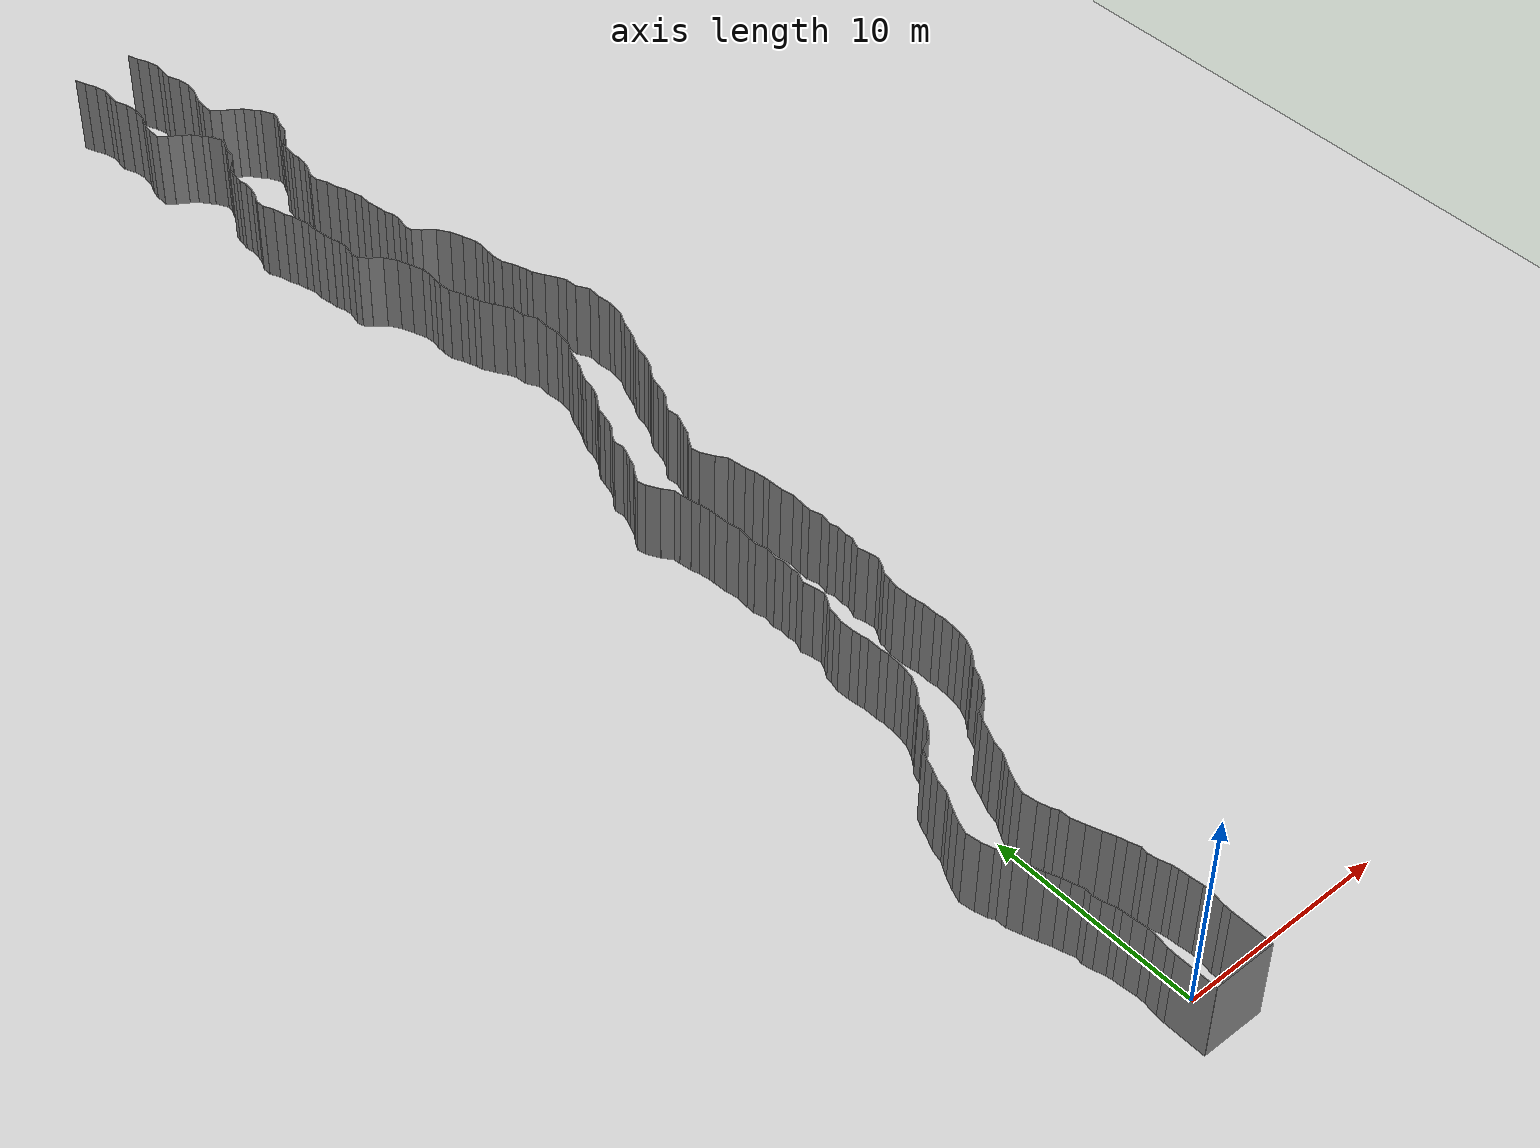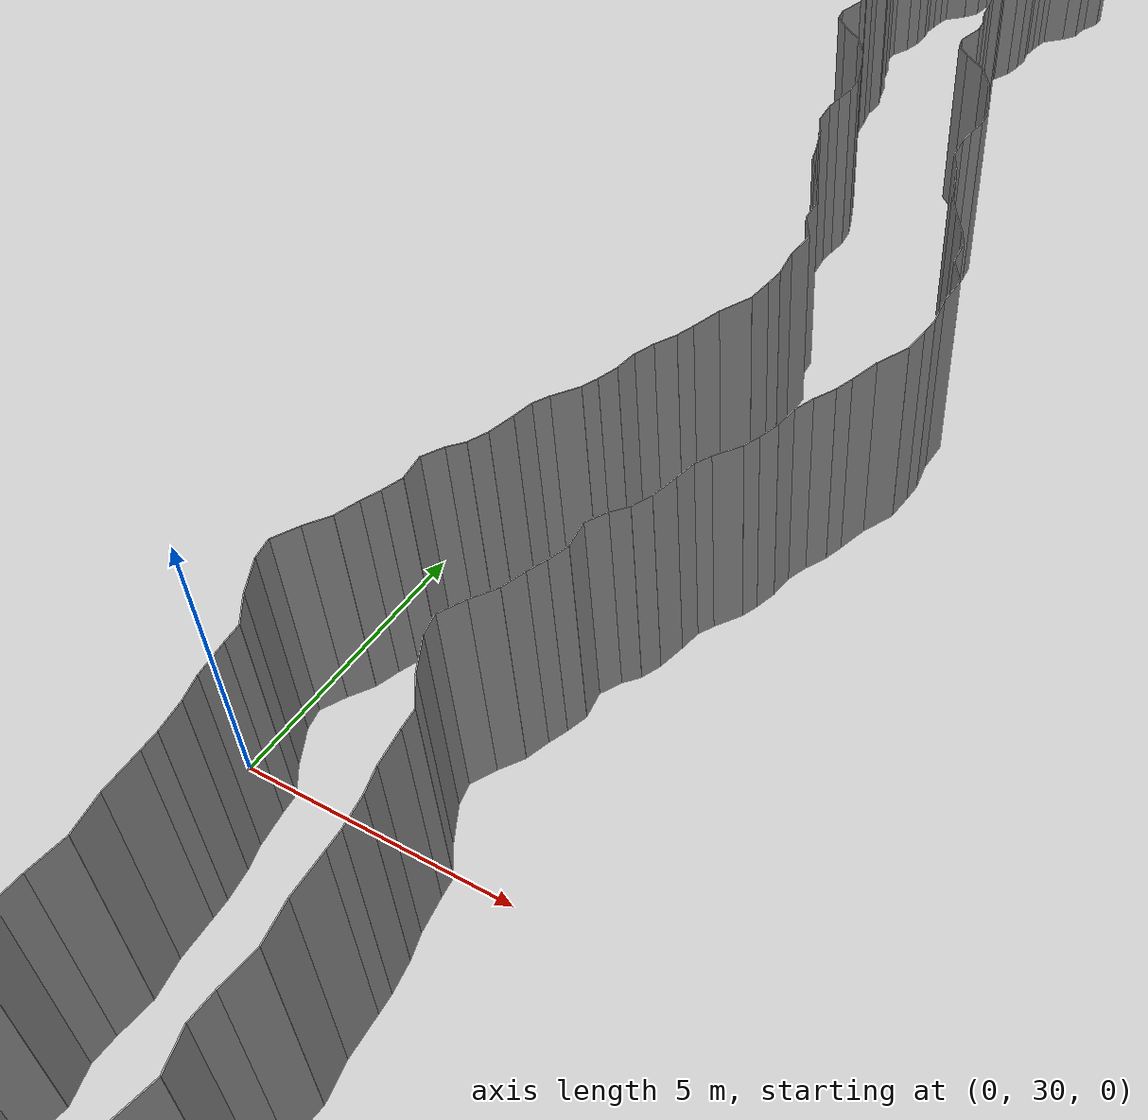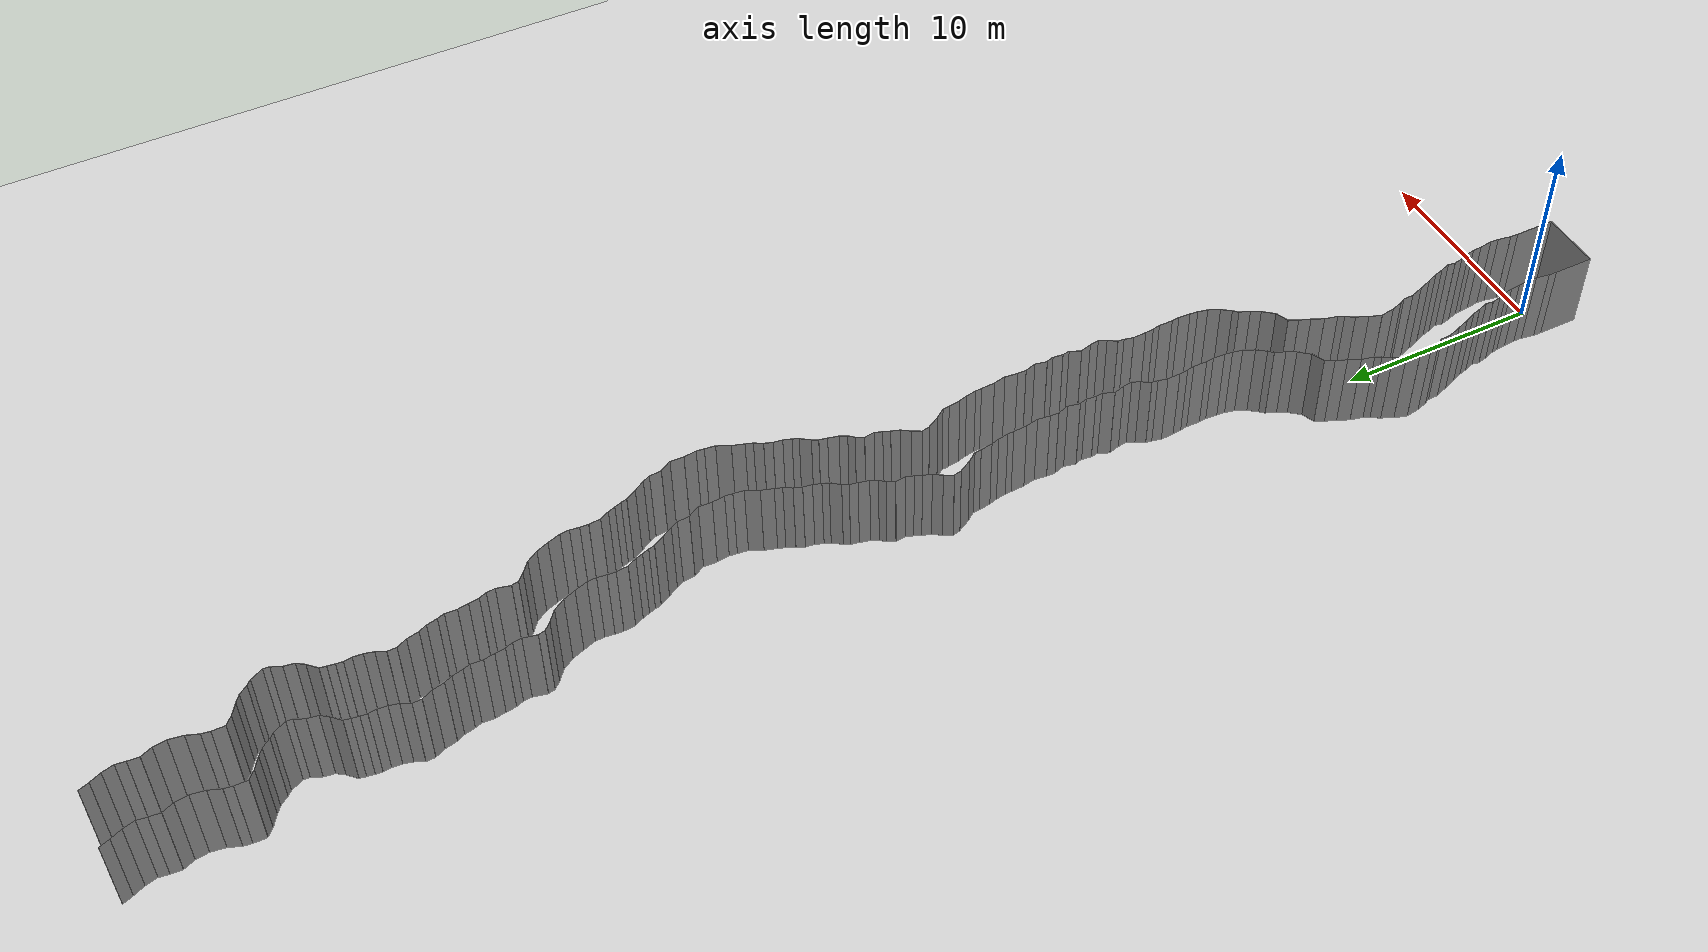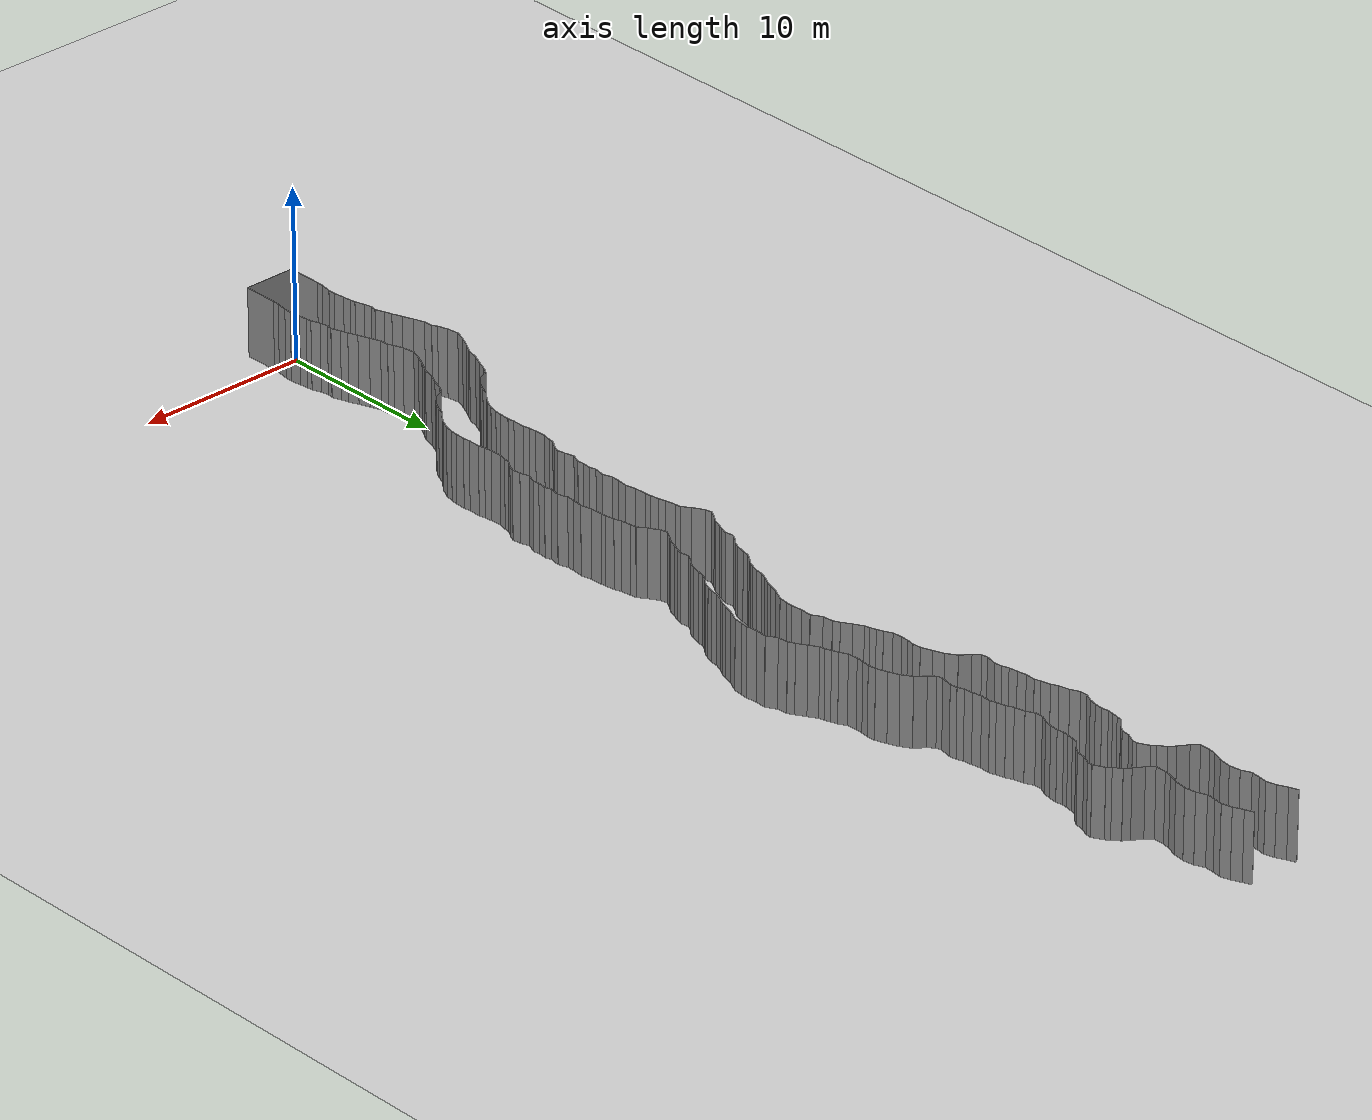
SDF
<sdf version="1.6">
 <world name="default">
  <light name="sun" type="directional">
   <pose>0 0 10 0 -0 0</pose>
   <diffuse>0.8 0.8 0.8 1</diffuse>
   <specular>0.2 0.2 0.2 1</specular>
   <attenuation>
    <range>1000</range>
    <constant>0.9</constant>
    <linear>0.01</linear>
    <quadratic>0.001</quadratic>
   </attenuation>
   <direction>-0.5 0.1 -0.9</direction>
  </light>
  <model name="ground_plane">
   <static>1</static>
   <link name="link">
    <collision name="collision">
     <geometry><plane><normal>0 0 1</normal><size>200 200</size></plane></geometry>
     <surface><friction><ode><mu>100</mu><mu2>50</mu2></ode></friction></surface>
    </collision>
    <visual name="visual">
     <cast_shadows>0</cast_shadows>
     <geometry><plane><normal>0 0 1</normal><size>200 200</size></plane></geometry>
     <material>
      <script><uri>file://media/materials/scripts/gazebo.material</uri><name>Gazebo/Grey</name></script>
     </material>
    </visual>
   </link>
   <pose>0 100 0 0 -0 0</pose>
  </model>
  <gravity>0 0 -9.8</gravity>
  <magnetic_field>6e-06 2.3e-05 -4.2e-05</magnetic_field>
  <atmosphere type="adiabatic"/>
  <physics default="0" name="default_physics" type="ode">
   <max_step_size>0.001</max_step_size>
   <real_time_factor>1</real_time_factor>
   <real_time_update_rate>1000</real_time_update_rate>
  </physics>
  <scene><ambient>0.4 0.4 0.4 1</ambient><background>0.7 0.7 0.7 1</background><shadows>1</shadows></scene>
  <spherical_coordinates>
   <surface_model>EARTH_WGS84</surface_model>
   <latitude_deg>0</latitude_deg>
   <longitude_deg>0</longitude_deg>
   <elevation>0</elevation>
   <heading_deg>0</heading_deg>
  </spherical_coordinates>
  <model name="wall_back">
   <static>1</static>
   <pose>0.0 -2 2 0.0 0 0.0</pose>
   <link name="link">
    <collision name="collision"><geometry><box><size>3 0.02 4</size></box></geometry></collision>
    <visual name="visual">
     <material>
      <script><name>Gazebo/Grey</name><uri>file://media/materials/scripts/gazebo.material</uri></script>
     </material>
     <geometry><box><size>3 0.02 4</size></box></geometry>
    </visual>
   </link>
  </model>
  <model name="wall_left">
   <static>1</static>
   <pose>1.5 -1 2 0 0 0.00</pose>
   <link name="link">
    <collision name="collision"><geometry><box><size>0.02 2 4</size></box></geometry></collision>
    <visual name="visual">
     <material>
      <script><name>Gazebo/Grey</name><uri>file://media/materials/scripts/gazebo.material</uri></script>
     </material>
     <geometry><box><size>0.02 2 4</size></box></geometry>
    </visual>
   </link>
  </model>
  <model name="wall_right">
   <static>1</static>
   <pose>-1.5 -1 2 0 0 0.00</pose>
   <link name="link">
    <collision name="collision"><geometry><box><size>0.02 2 4</size></box></geometry></collision>
    <visual name="visual">
     <material>
      <script><name>Gazebo/Grey</name><uri>file://media/materials/scripts/gazebo.material</uri></script>
     </material>
     <geometry><box><size>0.02 2 4</size></box></geometry>
    </visual>
   </link>
  </model>
  <model name="wall_0">
   <static>1</static>
   <pose>-1.489518586047968 0.20049732943710094 2 0 0 -0.05222953051110134</pose>
   <link name="link">
    <collision name="collision"><geometry><box><size>0.02 0.401542222686 4</size></box></geometry></collision>
    <visual name="visual">
     <material>
      <script><name>Gazebo/Grey</name><uri>file://media/materials/scripts/gazebo.material</uri></script>
     </material>
     <geometry><box><size>0.02 0.401542222686 4</size></box></geometry>
    </visual>
   </link>
  </model>
  <model name="wall_1">
   <static>1</static>
   <pose>1.510481413952032 0.20049732943710094 2 0 0 -0.05222953051110134</pose>
   <link name="link">
    <collision name="collision"><geometry><box><size>0.02 0.401542222686 4</size></box></geometry></collision>
    <visual name="visual">
     <material>
      <script><name>Gazebo/Grey</name><uri>file://media/materials/scripts/gazebo.material</uri></script>
     </material>
     <geometry><box><size>0.02 0.401542222686 4</size></box></geometry>
    </visual>
   </link>
  </model>
  <model name="wall_2">
   <static>1</static>
   <pose>-1.4214829470044996 0.7288020010732138 2 0 0 -0.17380190108897955</pose>
   <link name="link">
    <collision name="collision"><geometry><box><size>0.02 0.665642974651 4</size></box></geometry></collision>
    <visual name="visual">
     <material>
      <script><name>Gazebo/Grey</name><uri>file://media/materials/scripts/gazebo.material</uri></script>
     </material>
     <geometry><box><size>0.02 0.665642974651 4</size></box></geometry>
    </visual>
   </link>
  </model>
  <model name="wall_3">
   <static>1</static>
   <pose>1.5785170529955004 0.7288020010732138 2 0 0 -0.17380190108897955</pose>
   <link name="link">
    <collision name="collision"><geometry><box><size>0.02 0.665642974651 4</size></box></geometry></collision>
    <visual name="visual">
     <material>
      <script><name>Gazebo/Grey</name><uri>file://media/materials/scripts/gazebo.material</uri></script>
     </material>
     <geometry><box><size>0.02 0.665642974651 4</size></box></geometry>
    </visual>
   </link>
  </model>
  <model name="wall_4">
   <static>1</static>
   <pose>-1.3579543316731462 1.2718780024738132 2 0 0 -0.027746059586998134</pose>
   <link name="link">
    <collision name="collision"><geometry><box><size>0.02 0.430703094826 4</size></box></geometry></collision>
    <visual name="visual">
     <material>
      <script><name>Gazebo/Grey</name><uri>file://media/materials/scripts/gazebo.material</uri></script>
     </material>
     <geometry><box><size>0.02 0.430703094826 4</size></box></geometry>
    </visual>
   </link>
  </model>
  <model name="wall_5">
   <static>1</static>
   <pose>1.6420456683268538 1.2718780024738132 2 0 0 -0.027746059586998134</pose>
   <link name="link">
    <collision name="collision"><geometry><box><size>0.02 0.430703094826 4</size></box></geometry></collision>
    <visual name="visual">
     <material>
      <script><name>Gazebo/Grey</name><uri>file://media/materials/scripts/gazebo.material</uri></script>
     </material>
     <geometry><box><size>0.02 0.430703094826 4</size></box></geometry>
    </visual>
   </link>
  </model>
  <model name="wall_6">
   <static>1</static>
   <pose>-1.3885365490897117 1.8003926404126556 2 0 0 0.11617703816787787</pose>
   <link name="link">
    <collision name="collision"><geometry><box><size>0.02 0.630743779227 4</size></box></geometry></collision>
    <visual name="visual">
     <material>
      <script><name>Gazebo/Grey</name><uri>file://media/materials/scripts/gazebo.material</uri></script>
     </material>
     <geometry><box><size>0.02 0.630743779227 4</size></box></geometry>
    </visual>
   </link>
  </model>
  <model name="wall_7">
   <static>1</static>
   <pose>1.6114634509102883 1.8003926404126556 2 0 0 0.11617703816787787</pose>
   <link name="link">
    <collision name="collision"><geometry><box><size>0.02 0.630743779227 4</size></box></geometry></collision>
    <visual name="visual">
     <material>
      <script><name>Gazebo/Grey</name><uri>file://media/materials/scripts/gazebo.material</uri></script>
     </material>
     <geometry><box><size>0.02 0.630743779227 4</size></box></geometry>
    </visual>
   </link>
  </model>
  <model name="wall_8">
   <static>1</static>
   <pose>-1.4458201575018677 2.353512467075582 2 0 0 0.08619383034046935</pose>
   <link name="link">
    <collision name="collision"><geometry><box><size>0.02 0.481535342333 4</size></box></geometry></collision>
    <visual name="visual">
     <material>
      <script><name>Gazebo/Grey</name><uri>file://media/materials/scripts/gazebo.material</uri></script>
     </material>
     <geometry><box><size>0.02 0.481535342333 4</size></box></geometry>
    </visual>
   </link>
  </model>
  <model name="wall_9">
   <static>1</static>
   <pose>1.5541798424981323 2.353512467075582 2 0 0 0.08619383034046935</pose>
   <link name="link">
    <collision name="collision"><geometry><box><size>0.02 0.481535342333 4</size></box></geometry></collision>
    <visual name="visual">
     <material>
      <script><name>Gazebo/Grey</name><uri>file://media/materials/scripts/gazebo.material</uri></script>
     </material>
     <geometry><box><size>0.02 0.481535342333 4</size></box></geometry>
    </visual>
   </link>
  </model>
  <model name="wall_10">
   <static>1</static>
   <pose>-1.4889563472218057 2.7457335104750245 2 0 0 0.14604560094594113</pose>
   <link name="link">
    <collision name="collision"><geometry><box><size>0.02 0.307972984002 4</size></box></geometry></collision>
    <visual name="visual">
     <material>
      <script><name>Gazebo/Grey</name><uri>file://media/materials/scripts/gazebo.material</uri></script>
     </material>
     <geometry><box><size>0.02 0.307972984002 4</size></box></geometry>
    </visual>
   </link>
  </model>
  <model name="wall_11">
   <static>1</static>
   <pose>1.5110436527781943 2.7457335104750245 2 0 0 0.14604560094594113</pose>
   <link name="link">
    <collision name="collision"><geometry><box><size>0.02 0.307972984002 4</size></box></geometry></collision>
    <visual name="visual">
     <material>
      <script><name>Gazebo/Grey</name><uri>file://media/materials/scripts/gazebo.material</uri></script>
     </material>
     <geometry><box><size>0.02 0.307972984002 4</size></box></geometry>
    </visual>
   </link>
  </model>
  <model name="wall_12">
   <static>1</static>
   <pose>-1.596894082027641 3.158114141264798 2 0 0 0.31776757768315944</pose>
   <link name="link">
    <collision name="collision"><geometry><box><size>0.02 0.547476098605 4</size></box></geometry></collision>
    <visual name="visual">
     <material>
      <script><name>Gazebo/Grey</name><uri>file://media/materials/scripts/gazebo.material</uri></script>
     </material>
     <geometry><box><size>0.02 0.547476098605 4</size></box></geometry>
    </visual>
   </link>
  </model>
  <model name="wall_13">
   <static>1</static>
   <pose>1.403105917972359 3.158114141264798 2 0 0 0.31776757768315944</pose>
   <link name="link">
    <collision name="collision"><geometry><box><size>0.02 0.547476098605 4</size></box></geometry></collision>
    <visual name="visual">
     <material>
      <script><name>Gazebo/Grey</name><uri>file://media/materials/scripts/gazebo.material</uri></script>
     </material>
     <geometry><box><size>0.02 0.547476098605 4</size></box></geometry>
    </visual>
   </link>
  </model>
  <model name="wall_14">
   <static>1</static>
   <pose>-1.729432926856667 3.645361085510085 2 0 0 0.20402054347122936</pose>
   <link name="link">
    <collision name="collision"><geometry><box><size>0.02 0.46405149219 4</size></box></geometry></collision>
    <visual name="visual">
     <material>
      <script><name>Gazebo/Grey</name><uri>file://media/materials/scripts/gazebo.material</uri></script>
     </material>
     <geometry><box><size>0.02 0.46405149219 4</size></box></geometry>
    </visual>
   </link>
  </model>
  <model name="wall_15">
   <static>1</static>
   <pose>1.270567073143333 3.645361085510085 2 0 0 0.20402054347122936</pose>
   <link name="link">
    <collision name="collision"><geometry><box><size>0.02 0.46405149219 4</size></box></geometry></collision>
    <visual name="visual">
     <material>
      <script><name>Gazebo/Grey</name><uri>file://media/materials/scripts/gazebo.material</uri></script>
     </material>
     <geometry><box><size>0.02 0.46405149219 4</size></box></geometry>
    </visual>
   </link>
  </model>
  <model name="wall_16">
   <static>1</static>
   <pose>-1.74293647429722 4.046996853891628 2 0 0 -0.18978929705398656</pose>
   <link name="link">
    <collision name="collision"><geometry><box><size>0.02 0.35522289899 4</size></box></geometry></collision>
    <visual name="visual">
     <material>
      <script><name>Gazebo/Grey</name><uri>file://media/materials/scripts/gazebo.material</uri></script>
     </material>
     <geometry><box><size>0.02 0.35522289899 4</size></box></geometry>
    </visual>
   </link>
  </model>
  <model name="wall_17">
   <static>1</static>
   <pose>1.25706352570278 4.046996853891628 2 0 0 -0.18978929705398656</pose>
   <link name="link">
    <collision name="collision"><geometry><box><size>0.02 0.35522289899 4</size></box></geometry></collision>
    <visual name="visual">
     <material>
      <script><name>Gazebo/Grey</name><uri>file://media/materials/scripts/gazebo.material</uri></script>
     </material>
     <geometry><box><size>0.02 0.35522289899 4</size></box></geometry>
    </visual>
   </link>
  </model>
  <model name="wall_18">
   <static>1</static>
   <pose>-1.803507631129231 4.478444069290012 2 0 0 0.35088025179784704</pose>
   <link name="link">
    <collision name="collision"><geometry><box><size>0.02 0.547402889375 4</size></box></geometry></collision>
    <visual name="visual">
     <material>
      <script><name>Gazebo/Grey</name><uri>file://media/materials/scripts/gazebo.material</uri></script>
     </material>
     <geometry><box><size>0.02 0.547402889375 4</size></box></geometry>
    </visual>
   </link>
  </model>
  <model name="wall_19">
   <static>1</static>
   <pose>1.196492368870769 4.478444069290012 2 0 0 0.35088025179784704</pose>
   <link name="link">
    <collision name="collision"><geometry><box><size>0.02 0.547402889375 4</size></box></geometry></collision>
    <visual name="visual">
     <material>
      <script><name>Gazebo/Grey</name><uri>file://media/materials/scripts/gazebo.material</uri></script>
     </material>
     <geometry><box><size>0.02 0.547402889375 4</size></box></geometry>
    </visual>
   </link>
  </model>
  <model name="wall_20">
   <static>1</static>
   <pose>-1.9574651885111887 4.952137848123724 2 0 0 0.2696346675039881</pose>
   <link name="link">
    <collision name="collision"><geometry><box><size>0.02 0.449581810914 4</size></box></geometry></collision>
    <visual name="visual">
     <material>
      <script><name>Gazebo/Grey</name><uri>file://media/materials/scripts/gazebo.material</uri></script>
     </material>
     <geometry><box><size>0.02 0.449581810914 4</size></box></geometry>
    </visual>
   </link>
  </model>
  <model name="wall_21">
   <static>1</static>
   <pose>1.0425348114888113 4.952137848123724 2 0 0 0.2696346675039881</pose>
   <link name="link">
    <collision name="collision"><geometry><box><size>0.02 0.449581810914 4</size></box></geometry></collision>
    <visual name="visual">
     <material>
      <script><name>Gazebo/Grey</name><uri>file://media/materials/scripts/gazebo.material</uri></script>
     </material>
     <geometry><box><size>0.02 0.449581810914 4</size></box></geometry>
    </visual>
   </link>
  </model>
  <model name="wall_22">
   <static>1</static>
   <pose>-2.1256902756428024 5.43505233538048 2 0 0 0.3864729368121072</pose>
   <link name="link">
    <collision name="collision"><geometry><box><size>0.02 0.574892990942 4</size></box></geometry></collision>
    <visual name="visual">
     <material>
      <script><name>Gazebo/Grey</name><uri>file://media/materials/scripts/gazebo.material</uri></script>
     </material>
     <geometry><box><size>0.02 0.574892990942 4</size></box></geometry>
    </visual>
   </link>
  </model>
  <model name="wall_23">
   <static>1</static>
   <pose>0.8743097243571976 5.43505233538048 2 0 0 0.3864729368121072</pose>
   <link name="link">
    <collision name="collision"><geometry><box><size>0.02 0.574892990942 4</size></box></geometry></collision>
    <visual name="visual">
     <material>
      <script><name>Gazebo/Grey</name><uri>file://media/materials/scripts/gazebo.material</uri></script>
     </material>
     <geometry><box><size>0.02 0.574892990942 4</size></box></geometry>
    </visual>
   </link>
  </model>
  <model name="wall_24">
   <static>1</static>
   <pose>-2.3471178421616776 6.0121453797528535 2 0 0 0.3489037357054069</pose>
   <link name="link">
    <collision name="collision"><geometry><box><size>0.02 0.661554718572 4</size></box></geometry></collision>
    <visual name="visual">
     <material>
      <script><name>Gazebo/Grey</name><uri>file://media/materials/scripts/gazebo.material</uri></script>
     </material>
     <geometry><box><size>0.02 0.661554718572 4</size></box></geometry>
    </visual>
   </link>
  </model>
  <model name="wall_25">
   <static>1</static>
   <pose>0.6528821578383224 6.0121453797528535 2 0 0 0.3489037357054069</pose>
   <link name="link">
    <collision name="collision"><geometry><box><size>0.02 0.661554718572 4</size></box></geometry></collision>
    <visual name="visual">
     <material>
      <script><name>Gazebo/Grey</name><uri>file://media/materials/scripts/gazebo.material</uri></script>
     </material>
     <geometry><box><size>0.02 0.661554718572 4</size></box></geometry>
    </visual>
   </link>
  </model>
  <model name="wall_26">
   <static>1</static>
   <pose>-2.5667578166942926 6.63271991162041 2 0 0 0.3313534349744455</pose>
   <link name="link">
    <collision name="collision"><geometry><box><size>0.02 0.655089255526 4</size></box></geometry></collision>
    <visual name="visual">
     <material>
      <script><name>Gazebo/Grey</name><uri>file://media/materials/scripts/gazebo.material</uri></script>
     </material>
     <geometry><box><size>0.02 0.655089255526 4</size></box></geometry>
    </visual>
   </link>
  </model>
  <model name="wall_27">
   <static>1</static>
   <pose>0.4332421833057074 6.63271991162041 2 0 0 0.3313534349744455</pose>
   <link name="link">
    <collision name="collision"><geometry><box><size>0.02 0.655089255526 4</size></box></geometry></collision>
    <visual name="visual">
     <material>
      <script><name>Gazebo/Grey</name><uri>file://media/materials/scripts/gazebo.material</uri></script>
     </material>
     <geometry><box><size>0.02 0.655089255526 4</size></box></geometry>
    </visual>
   </link>
  </model>
  <model name="wall_28">
   <static>1</static>
   <pose>-2.6817052931690473 7.202625932338233 2 0 0 0.032234456207765</pose>
   <link name="link">
    <collision name="collision"><geometry><box><size>0.02 0.520628196297 4</size></box></geometry></collision>
    <visual name="visual">
     <material>
      <script><name>Gazebo/Grey</name><uri>file://media/materials/scripts/gazebo.material</uri></script>
     </material>
     <geometry><box><size>0.02 0.520628196297 4</size></box></geometry>
    </visual>
   </link>
  </model>
  <model name="wall_29">
   <static>1</static>
   <pose>0.31829470683095273 7.202625932338233 2 0 0 0.032234456207765</pose>
   <link name="link">
    <collision name="collision"><geometry><box><size>0.02 0.520628196297 4</size></box></geometry></collision>
    <visual name="visual">
     <material>
      <script><name>Gazebo/Grey</name><uri>file://media/materials/scripts/gazebo.material</uri></script>
     </material>
     <geometry><box><size>0.02 0.520628196297 4</size></box></geometry>
    </visual>
   </link>
  </model>
  <model name="wall_30">
   <static>1</static>
   <pose>-2.768281006672819 7.602706860975515 2 0 0 0.5096223330162535</pose>
   <link name="link">
    <collision name="collision"><geometry><box><size>0.02 0.320534865083 4</size></box></geometry></collision>
    <visual name="visual">
     <material>
      <script><name>Gazebo/Grey</name><uri>file://media/materials/scripts/gazebo.material</uri></script>
     </material>
     <geometry><box><size>0.02 0.320534865083 4</size></box></geometry>
    </visual>
   </link>
  </model>
  <model name="wall_31">
   <static>1</static>
   <pose>0.23171899332718082 7.602706860975515 2 0 0 0.5096223330162535</pose>
   <link name="link">
    <collision name="collision"><geometry><box><size>0.02 0.320534865083 4</size></box></geometry></collision>
    <visual name="visual">
     <material>
      <script><name>Gazebo/Grey</name><uri>file://media/materials/scripts/gazebo.material</uri></script>
     </material>
     <geometry><box><size>0.02 0.320534865083 4</size></box></geometry>
    </visual>
   </link>
  </model>
  <model name="wall_32">
   <static>1</static>
   <pose>-2.9284501335781075 8.01551304571727 2 0 0 0.29183261499156843</pose>
   <link name="link">
    <collision name="collision"><geometry><box><size>0.02 0.569904837245 4</size></box></geometry></collision>
    <visual name="visual">
     <material>
      <script><name>Gazebo/Grey</name><uri>file://media/materials/scripts/gazebo.material</uri></script>
     </material>
     <geometry><box><size>0.02 0.569904837245 4</size></box></geometry>
    </visual>
   </link>
  </model>
  <model name="wall_33">
   <static>1</static>
   <pose>0.07154986642189254 8.01551304571727 2 0 0 0.29183261499156843</pose>
   <link name="link">
    <collision name="collision"><geometry><box><size>0.02 0.569904837245 4</size></box></geometry></collision>
    <visual name="visual">
     <material>
      <script><name>Gazebo/Grey</name><uri>file://media/materials/scripts/gazebo.material</uri></script>
     </material>
     <geometry><box><size>0.02 0.569904837245 4</size></box></geometry>
    </visual>
   </link>
  </model>
  <model name="wall_34">
   <static>1</static>
   <pose>-3.0642480951425792 8.63425046036749 2 0 0 0.15437136792551523</pose>
   <link name="link">
    <collision name="collision"><geometry><box><size>0.02 0.69999059891 4</size></box></geometry></collision>
    <visual name="visual">
     <material>
      <script><name>Gazebo/Grey</name><uri>file://media/materials/scripts/gazebo.material</uri></script>
     </material>
     <geometry><box><size>0.02 0.69999059891 4</size></box></geometry>
    </visual>
   </link>
  </model>
  <model name="wall_35">
   <static>1</static>
   <pose>-0.06424809514257923 8.63425046036749 2 0 0 0.15437136792551523</pose>
   <link name="link">
    <collision name="collision"><geometry><box><size>0.02 0.69999059891 4</size></box></geometry></collision>
    <visual name="visual">
     <material>
      <script><name>Gazebo/Grey</name><uri>file://media/materials/scripts/gazebo.material</uri></script>
     </material>
     <geometry><box><size>0.02 0.69999059891 4</size></box></geometry>
    </visual>
   </link>
  </model>
  <model name="wall_36">
   <static>1</static>
   <pose>-3.010063837320274 9.277765566784698 2 0 0 -0.34803275006501383</pose>
   <link name="link">
    <collision name="collision"><geometry><box><size>0.02 0.633334938087 4</size></box></geometry></collision>
    <visual name="visual">
     <material>
      <script><name>Gazebo/Grey</name><uri>file://media/materials/scripts/gazebo.material</uri></script>
     </material>
     <geometry><box><size>0.02 0.633334938087 4</size></box></geometry>
    </visual>
   </link>
  </model>
  <model name="wall_37">
   <static>1</static>
   <pose>-0.01006383732027416 9.277765566784698 2 0 0 -0.34803275006501383</pose>
   <link name="link">
    <collision name="collision"><geometry><box><size>0.02 0.633334938087 4</size></box></geometry></collision>
    <visual name="visual">
     <material>
      <script><name>Gazebo/Grey</name><uri>file://media/materials/scripts/gazebo.material</uri></script>
     </material>
     <geometry><box><size>0.02 0.633334938087 4</size></box></geometry>
    </visual>
   </link>
  </model>
  <model name="wall_38">
   <static>1</static>
   <pose>-2.7705077600563 9.858821510863308 2 0 0 -0.4346421779830581</pose>
   <link name="link">
    <collision name="collision"><geometry><box><size>0.02 0.624845947142 4</size></box></geometry></collision>
    <visual name="visual">
     <material>
      <script><name>Gazebo/Grey</name><uri>file://media/materials/scripts/gazebo.material</uri></script>
     </material>
     <geometry><box><size>0.02 0.624845947142 4</size></box></geometry>
    </visual>
   </link>
  </model>
  <model name="wall_39">
   <static>1</static>
   <pose>0.22949223994370005 9.858821510863308 2 0 0 -0.4346421779830581</pose>
   <link name="link">
    <collision name="collision"><geometry><box><size>0.02 0.624845947142 4</size></box></geometry></collision>
    <visual name="visual">
     <material>
      <script><name>Gazebo/Grey</name><uri>file://media/materials/scripts/gazebo.material</uri></script>
     </material>
     <geometry><box><size>0.02 0.624845947142 4</size></box></geometry>
    </visual>
   </link>
  </model>
  <model name="wall_40">
   <static>1</static>
   <pose>-2.514608879797339 10.361208416488681 2 0 0 -0.5163599203486481</pose>
   <link name="link">
    <collision name="collision"><geometry><box><size>0.02 0.503696435168 4</size></box></geometry></collision>
    <visual name="visual">
     <material>
      <script><name>Gazebo/Grey</name><uri>file://media/materials/scripts/gazebo.material</uri></script>
     </material>
     <geometry><box><size>0.02 0.503696435168 4</size></box></geometry>
    </visual>
   </link>
  </model>
  <model name="wall_41">
   <static>1</static>
   <pose>0.48539112020266106 10.361208416488681 2 0 0 -0.5163599203486481</pose>
   <link name="link">
    <collision name="collision"><geometry><box><size>0.02 0.503696435168 4</size></box></geometry></collision>
    <visual name="visual">
     <material>
      <script><name>Gazebo/Grey</name><uri>file://media/materials/scripts/gazebo.material</uri></script>
     </material>
     <geometry><box><size>0.02 0.503696435168 4</size></box></geometry>
    </visual>
   </link>
  </model>
  <model name="wall_42">
   <static>1</static>
   <pose>-2.309268981880272 10.722486312490199 2 0 0 -0.5175739369132143</pose>
   <link name="link">
    <collision name="collision"><geometry><box><size>0.02 0.327414273657 4</size></box></geometry></collision>
    <visual name="visual">
     <material>
      <script><name>Gazebo/Grey</name><uri>file://media/materials/scripts/gazebo.material</uri></script>
     </material>
     <geometry><box><size>0.02 0.327414273657 4</size></box></geometry>
    </visual>
   </link>
  </model>
  <model name="wall_43">
   <static>1</static>
   <pose>0.6907310181197279 10.722486312490199 2 0 0 -0.5175739369132143</pose>
   <link name="link">
    <collision name="collision"><geometry><box><size>0.02 0.327414273657 4</size></box></geometry></collision>
    <visual name="visual">
     <material>
      <script><name>Gazebo/Grey</name><uri>file://media/materials/scripts/gazebo.material</uri></script>
     </material>
     <geometry><box><size>0.02 0.327414273657 4</size></box></geometry>
    </visual>
   </link>
  </model>
  <model name="wall_44">
   <static>1</static>
   <pose>-2.151062313754524 11.17653106160025 2 0 0 -0.24275517112561143</pose>
   <link name="link">
    <collision name="collision"><geometry><box><size>0.02 0.64239467446 4</size></box></geometry></collision>
    <visual name="visual">
     <material>
      <script><name>Gazebo/Grey</name><uri>file://media/materials/scripts/gazebo.material</uri></script>
     </material>
     <geometry><box><size>0.02 0.64239467446 4</size></box></geometry>
    </visual>
   </link>
  </model>
  <model name="wall_45">
   <static>1</static>
   <pose>0.8489376862454758 11.17653106160025 2 0 0 -0.24275517112561143</pose>
   <link name="link">
    <collision name="collision"><geometry><box><size>0.02 0.64239467446 4</size></box></geometry></collision>
    <visual name="visual">
     <material>
      <script><name>Gazebo/Grey</name><uri>file://media/materials/scripts/gazebo.material</uri></script>
     </material>
     <geometry><box><size>0.02 0.64239467446 4</size></box></geometry>
    </visual>
   </link>
  </model>
  <model name="wall_46">
   <static>1</static>
   <pose>-1.936993852102987 11.77434045904762 2 0 0 -0.44628441364280985</pose>
   <link name="link">
    <collision name="collision"><geometry><box><size>0.02 0.634172241785 4</size></box></geometry></collision>
    <visual name="visual">
     <material>
      <script><name>Gazebo/Grey</name><uri>file://media/materials/scripts/gazebo.material</uri></script>
     </material>
     <geometry><box><size>0.02 0.634172241785 4</size></box></geometry>
    </visual>
   </link>
  </model>
  <model name="wall_47">
   <static>1</static>
   <pose>1.063006147897013 11.77434045904762 2 0 0 -0.44628441364280985</pose>
   <link name="link">
    <collision name="collision"><geometry><box><size>0.02 0.634172241785 4</size></box></geometry></collision>
    <visual name="visual">
     <material>
      <script><name>Gazebo/Grey</name><uri>file://media/materials/scripts/gazebo.material</uri></script>
     </material>
     <geometry><box><size>0.02 0.634172241785 4</size></box></geometry>
    </visual>
   </link>
  </model>
  <model name="wall_48">
   <static>1</static>
   <pose>-1.697552183234039 12.331902202936323 2 0 0 -0.36121409726074083</pose>
   <link name="link">
    <collision name="collision"><geometry><box><size>0.02 0.580526218845 4</size></box></geometry></collision>
    <visual name="visual">
     <material>
      <script><name>Gazebo/Grey</name><uri>file://media/materials/scripts/gazebo.material</uri></script>
     </material>
     <geometry><box><size>0.02 0.580526218845 4</size></box></geometry>
    </visual>
   </link>
  </model>
  <model name="wall_49">
   <static>1</static>
   <pose>1.302447816765961 12.331902202936323 2 0 0 -0.36121409726074083</pose>
   <link name="link">
    <collision name="collision"><geometry><box><size>0.02 0.580526218845 4</size></box></geometry></collision>
    <visual name="visual">
     <material>
      <script><name>Gazebo/Grey</name><uri>file://media/materials/scripts/gazebo.material</uri></script>
     </material>
     <geometry><box><size>0.02 0.580526218845 4</size></box></geometry>
    </visual>
   </link>
  </model>
  <model name="wall_50">
   <static>1</static>
   <pose>-1.4797514190591698 12.819096526967375 2 0 0 -0.4906750498373535</pose>
   <link name="link">
    <collision name="collision"><geometry><box><size>0.02 0.489021968066 4</size></box></geometry></collision>
    <visual name="visual">
     <material>
      <script><name>Gazebo/Grey</name><uri>file://media/materials/scripts/gazebo.material</uri></script>
     </material>
     <geometry><box><size>0.02 0.489021968066 4</size></box></geometry>
    </visual>
   </link>
  </model>
  <model name="wall_51">
   <static>1</static>
   <pose>1.5202485809408302 12.819096526967375 2 0 0 -0.4906750498373535</pose>
   <link name="link">
    <collision name="collision"><geometry><box><size>0.02 0.489021968066 4</size></box></geometry></collision>
    <visual name="visual">
     <material>
      <script><name>Gazebo/Grey</name><uri>file://media/materials/scripts/gazebo.material</uri></script>
     </material>
     <geometry><box><size>0.02 0.489021968066 4</size></box></geometry>
    </visual>
   </link>
  </model>
  <model name="wall_52">
   <static>1</static>
   <pose>-1.0564365355146577 13.167485831337268 2 0 0 -1.1640255774593515</pose>
   <link name="link">
    <collision name="collision"><geometry><box><size>0.02 0.670938557921 4</size></box></geometry></collision>
    <visual name="visual">
     <material>
      <script><name>Gazebo/Grey</name><uri>file://media/materials/scripts/gazebo.material</uri></script>
     </material>
     <geometry><box><size>0.02 0.670938557921 4</size></box></geometry>
    </visual>
   </link>
  </model>
  <model name="wall_53">
   <static>1</static>
   <pose>1.9435634644853423 13.167485831337268 2 0 0 -1.1640255774593515</pose>
   <link name="link">
    <collision name="collision"><geometry><box><size>0.02 0.670938557921 4</size></box></geometry></collision>
    <visual name="visual">
     <material>
      <script><name>Gazebo/Grey</name><uri>file://media/materials/scripts/gazebo.material</uri></script>
     </material>
     <geometry><box><size>0.02 0.670938557921 4</size></box></geometry>
    </visual>
   </link>
  </model>
  <model name="wall_54">
   <static>1</static>
   <pose>-0.5287862599145199 13.564390611673788 2 0 0 -0.693409866530334</pose>
   <link name="link">
    <collision name="collision"><geometry><box><size>0.02 0.687005002998 4</size></box></geometry></collision>
    <visual name="visual">
     <material>
      <script><name>Gazebo/Grey</name><uri>file://media/materials/scripts/gazebo.material</uri></script>
     </material>
     <geometry><box><size>0.02 0.687005002998 4</size></box></geometry>
    </visual>
   </link>
  </model>
  <model name="wall_55">
   <static>1</static>
   <pose>2.47121374008548 13.564390611673788 2 0 0 -0.693409866530334</pose>
   <link name="link">
    <collision name="collision"><geometry><box><size>0.02 0.687005002998 4</size></box></geometry></collision>
    <visual name="visual">
     <material>
      <script><name>Gazebo/Grey</name><uri>file://media/materials/scripts/gazebo.material</uri></script>
     </material>
     <geometry><box><size>0.02 0.687005002998 4</size></box></geometry>
    </visual>
   </link>
  </model>
  <model name="wall_56">
   <static>1</static>
   <pose>-0.18669444980762256 14.049349786628886 2 0 0 -0.506687585451164</pose>
   <link name="link">
    <collision name="collision"><geometry><box><size>0.02 0.505014342716 4</size></box></geometry></collision>
    <visual name="visual">
     <material>
      <script><name>Gazebo/Grey</name><uri>file://media/materials/scripts/gazebo.material</uri></script>
     </material>
     <geometry><box><size>0.02 0.505014342716 4</size></box></geometry>
    </visual>
   </link>
  </model>
  <model name="wall_57">
   <static>1</static>
   <pose>2.8133055501923776 14.049349786628886 2 0 0 -0.506687585451164</pose>
   <link name="link">
    <collision name="collision"><geometry><box><size>0.02 0.505014342716 4</size></box></geometry></collision>
    <visual name="visual">
     <material>
      <script><name>Gazebo/Grey</name><uri>file://media/materials/scripts/gazebo.material</uri></script>
     </material>
     <geometry><box><size>0.02 0.505014342716 4</size></box></geometry>
    </visual>
   </link>
  </model>
  <model name="wall_58">
   <static>1</static>
   <pose>0.03686490835968653 14.519948339182639 2 0 0 -0.38427882856072476</pose>
   <link name="link">
    <collision name="collision"><geometry><box><size>0.02 0.538939799666 4</size></box></geometry></collision>
    <visual name="visual">
     <material>
      <script><name>Gazebo/Grey</name><uri>file://media/materials/scripts/gazebo.material</uri></script>
     </material>
     <geometry><box><size>0.02 0.538939799666 4</size></box></geometry>
    </visual>
   </link>
  </model>
  <model name="wall_59">
   <static>1</static>
   <pose>3.0368649083596866 14.519948339182639 2 0 0 -0.38427882856072476</pose>
   <link name="link">
    <collision name="collision"><geometry><box><size>0.02 0.538939799666 4</size></box></geometry></collision>
    <visual name="visual">
     <material>
      <script><name>Gazebo/Grey</name><uri>file://media/materials/scripts/gazebo.material</uri></script>
     </material>
     <geometry><box><size>0.02 0.538939799666 4</size></box></geometry>
    </visual>
   </link>
  </model>
  <model name="wall_60">
   <static>1</static>
   <pose>0.24548544720612056 14.884622924058446 2 0 0 -0.7527804125848092</pose>
   <link name="link">
    <collision name="collision"><geometry><box><size>0.02 0.314767969509 4</size></box></geometry></collision>
    <visual name="visual">
     <material>
      <script><name>Gazebo/Grey</name><uri>file://media/materials/scripts/gazebo.material</uri></script>
     </material>
     <geometry><box><size>0.02 0.314767969509 4</size></box></geometry>
    </visual>
   </link>
  </model>
  <model name="wall_61">
   <static>1</static>
   <pose>3.2454854472061205 14.884622924058446 2 0 0 -0.7527804125848092</pose>
   <link name="link">
    <collision name="collision"><geometry><box><size>0.02 0.314767969509 4</size></box></geometry></collision>
    <visual name="visual">
     <material>
      <script><name>Gazebo/Grey</name><uri>file://media/materials/scripts/gazebo.material</uri></script>
     </material>
     <geometry><box><size>0.02 0.314767969509 4</size></box></geometry>
    </visual>
   </link>
  </model>
  <model name="wall_62">
   <static>1</static>
   <pose>0.5168916326630328 15.220959239860585 2 0 0 -0.6368164197256273</pose>
   <link name="link">
    <collision name="collision"><geometry><box><size>0.02 0.550947472432 4</size></box></geometry></collision>
    <visual name="visual">
     <material>
      <script><name>Gazebo/Grey</name><uri>file://media/materials/scripts/gazebo.material</uri></script>
     </material>
     <geometry><box><size>0.02 0.550947472432 4</size></box></geometry>
    </visual>
   </link>
  </model>
  <model name="wall_63">
   <static>1</static>
   <pose>3.516891632663033 15.220959239860585 2 0 0 -0.6368164197256273</pose>
   <link name="link">
    <collision name="collision"><geometry><box><size>0.02 0.550947472432 4</size></box></geometry></collision>
    <visual name="visual">
     <material>
      <script><name>Gazebo/Grey</name><uri>file://media/materials/scripts/gazebo.material</uri></script>
     </material>
     <geometry><box><size>0.02 0.550947472432 4</size></box></geometry>
    </visual>
   </link>
  </model>
  <model name="wall_64">
   <static>1</static>
   <pose>0.8074883862494832 15.71108306155679 2 0 0 -0.44096418405069815</pose>
   <link name="link">
    <collision name="collision"><geometry><box><size>0.02 0.594123283342 4</size></box></geometry></collision>
    <visual name="visual">
     <material>
      <script><name>Gazebo/Grey</name><uri>file://media/materials/scripts/gazebo.material</uri></script>
     </material>
     <geometry><box><size>0.02 0.594123283342 4</size></box></geometry>
    </visual>
   </link>
  </model>
  <model name="wall_65">
   <static>1</static>
   <pose>3.8074883862494833 15.71108306155679 2 0 0 -0.44096418405069815</pose>
   <link name="link">
    <collision name="collision"><geometry><box><size>0.02 0.594123283342 4</size></box></geometry></collision>
    <visual name="visual">
     <material>
      <script><name>Gazebo/Grey</name><uri>file://media/materials/scripts/gazebo.material</uri></script>
     </material>
     <geometry><box><size>0.02 0.594123283342 4</size></box></geometry>
    </visual>
   </link>
  </model>
  <model name="wall_66">
   <static>1</static>
   <pose>0.9870611869444803 16.221256488551138 2 0 0 -0.2151564734587573</pose>
   <link name="link">
    <collision name="collision"><geometry><box><size>0.02 0.494457785638 4</size></box></geometry></collision>
    <visual name="visual">
     <material>
      <script><name>Gazebo/Grey</name><uri>file://media/materials/scripts/gazebo.material</uri></script>
     </material>
     <geometry><box><size>0.02 0.494457785638 4</size></box></geometry>
    </visual>
   </link>
  </model>
  <model name="wall_67">
   <static>1</static>
   <pose>3.98706118694448 16.221256488551138 2 0 0 -0.2151564734587573</pose>
   <link name="link">
    <collision name="collision"><geometry><box><size>0.02 0.494457785638 4</size></box></geometry></collision>
    <visual name="visual">
     <material>
      <script><name>Gazebo/Grey</name><uri>file://media/materials/scripts/gazebo.material</uri></script>
     </material>
     <geometry><box><size>0.02 0.494457785638 4</size></box></geometry>
    </visual>
   </link>
  </model>
  <model name="wall_68">
   <static>1</static>
   <pose>1.060250691287032 16.66250870103368 2 0 0 -0.10181816123662218</pose>
   <link name="link">
    <collision name="collision"><geometry><box><size>0.02 0.401526857537 4</size></box></geometry></collision>
    <visual name="visual">
     <material>
      <script><name>Gazebo/Grey</name><uri>file://media/materials/scripts/gazebo.material</uri></script>
     </material>
     <geometry><box><size>0.02 0.401526857537 4</size></box></geometry>
    </visual>
   </link>
  </model>
  <model name="wall_69">
   <static>1</static>
   <pose>4.060250691287032 16.66250870103368 2 0 0 -0.10181816123662218</pose>
   <link name="link">
    <collision name="collision"><geometry><box><size>0.02 0.401526857537 4</size></box></geometry></collision>
    <visual name="visual">
     <material>
      <script><name>Gazebo/Grey</name><uri>file://media/materials/scripts/gazebo.material</uri></script>
     </material>
     <geometry><box><size>0.02 0.401526857537 4</size></box></geometry>
    </visual>
   </link>
  </model>
  <model name="wall_70">
   <static>1</static>
   <pose>1.0986224788151837 17.157962579322703 2 0 0 -0.06067581981791525</pose>
   <link name="link">
    <collision name="collision"><geometry><box><size>0.02 0.592550823269 4</size></box></geometry></collision>
    <visual name="visual">
     <material>
      <script><name>Gazebo/Grey</name><uri>file://media/materials/scripts/gazebo.material</uri></script>
     </material>
     <geometry><box><size>0.02 0.592550823269 4</size></box></geometry>
    </visual>
   </link>
  </model>
  <model name="wall_71">
   <static>1</static>
   <pose>4.098622478815184 17.157962579322703 2 0 0 -0.06067581981791525</pose>
   <link name="link">
    <collision name="collision"><geometry><box><size>0.02 0.592550823269 4</size></box></geometry></collision>
    <visual name="visual">
     <material>
      <script><name>Gazebo/Grey</name><uri>file://media/materials/scripts/gazebo.material</uri></script>
     </material>
     <geometry><box><size>0.02 0.592550823269 4</size></box></geometry>
    </visual>
   </link>
  </model>
  <model name="wall_72">
   <static>1</static>
   <pose>1.0926212826150334 17.648242752760275 2 0 0 0.12257401669416847</pose>
   <link name="link">
    <collision name="collision"><geometry><box><size>0.02 0.392041348736 4</size></box></geometry></collision>
    <visual name="visual">
     <material>
      <script><name>Gazebo/Grey</name><uri>file://media/materials/scripts/gazebo.material</uri></script>
     </material>
     <geometry><box><size>0.02 0.392041348736 4</size></box></geometry>
    </visual>
   </link>
  </model>
  <model name="wall_73">
   <static>1</static>
   <pose>4.092621282615033 17.648242752760275 2 0 0 0.12257401669416847</pose>
   <link name="link">
    <collision name="collision"><geometry><box><size>0.02 0.392041348736 4</size></box></geometry></collision>
    <visual name="visual">
     <material>
      <script><name>Gazebo/Grey</name><uri>file://media/materials/scripts/gazebo.material</uri></script>
     </material>
     <geometry><box><size>0.02 0.392041348736 4</size></box></geometry>
    </visual>
   </link>
  </model>
  <model name="wall_74">
   <static>1</static>
   <pose>1.0732388111341435 18.187690049476906 2 0 0 -0.013291433530990255</pose>
   <link name="link">
    <collision name="collision"><geometry><box><size>0.02 0.689855584977 4</size></box></geometry></collision>
    <visual name="visual">
     <material>
      <script><name>Gazebo/Grey</name><uri>file://media/materials/scripts/gazebo.material</uri></script>
     </material>
     <geometry><box><size>0.02 0.689855584977 4</size></box></geometry>
    </visual>
   </link>
  </model>
  <model name="wall_75">
   <static>1</static>
   <pose>4.073238811134144 18.187690049476906 2 0 0 -0.013291433530990255</pose>
   <link name="link">
    <collision name="collision"><geometry><box><size>0.02 0.689855584977 4</size></box></geometry></collision>
    <visual name="visual">
     <material>
      <script><name>Gazebo/Grey</name><uri>file://media/materials/scripts/gazebo.material</uri></script>
     </material>
     <geometry><box><size>0.02 0.689855584977 4</size></box></geometry>
    </visual>
   </link>
  </model>
  <model name="wall_76">
   <static>1</static>
   <pose>1.0426178718898724 18.718711920294794 2 0 0 0.18694107810248098</pose>
   <link name="link">
    <collision name="collision"><geometry><box><size>0.02 0.378849658545 4</size></box></geometry></collision>
    <visual name="visual">
     <material>
      <script><name>Gazebo/Grey</name><uri>file://media/materials/scripts/gazebo.material</uri></script>
     </material>
     <geometry><box><size>0.02 0.378849658545 4</size></box></geometry>
    </visual>
   </link>
  </model>
  <model name="wall_77">
   <static>1</static>
   <pose>4.042617871889872 18.718711920294794 2 0 0 0.18694107810248098</pose>
   <link name="link">
    <collision name="collision"><geometry><box><size>0.02 0.378849658545 4</size></box></geometry></collision>
    <visual name="visual">
     <material>
      <script><name>Gazebo/Grey</name><uri>file://media/materials/scripts/gazebo.material</uri></script>
     </material>
     <geometry><box><size>0.02 0.378849658545 4</size></box></geometry>
    </visual>
   </link>
  </model>
  <model name="wall_78">
   <static>1</static>
   <pose>0.984165804529893 19.12431182267841 2 0 0 0.10552585542111075</pose>
   <link name="link">
    <collision name="collision"><geometry><box><size>0.02 0.44140611789 4</size></box></geometry></collision>
    <visual name="visual">
     <material>
      <script><name>Gazebo/Grey</name><uri>file://media/materials/scripts/gazebo.material</uri></script>
     </material>
     <geometry><box><size>0.02 0.44140611789 4</size></box></geometry>
    </visual>
   </link>
  </model>
  <model name="wall_79">
   <static>1</static>
   <pose>3.984165804529893 19.12431182267841 2 0 0 0.10552585542111075</pose>
   <link name="link">
    <collision name="collision"><geometry><box><size>0.02 0.44140611789 4</size></box></geometry></collision>
    <visual name="visual">
     <material>
      <script><name>Gazebo/Grey</name><uri>file://media/materials/scripts/gazebo.material</uri></script>
     </material>
     <geometry><box><size>0.02 0.44140611789 4</size></box></geometry>
    </visual>
   </link>
  </model>
  <model name="wall_80">
   <static>1</static>
   <pose>0.9522264733393769 19.66814566279179 2 0 0 0.026793110684806543</pose>
   <link name="link">
    <collision name="collision"><geometry><box><size>0.02 0.648949884071 4</size></box></geometry></collision>
    <visual name="visual">
     <material>
      <script><name>Gazebo/Grey</name><uri>file://media/materials/scripts/gazebo.material</uri></script>
     </material>
     <geometry><box><size>0.02 0.648949884071 4</size></box></geometry>
    </visual>
   </link>
  </model>
  <model name="wall_81">
   <static>1</static>
   <pose>3.952226473339377 19.66814566279179 2 0 0 0.026793110684806543</pose>
   <link name="link">
    <collision name="collision"><geometry><box><size>0.02 0.648949884071 4</size></box></geometry></collision>
    <visual name="visual">
     <material>
      <script><name>Gazebo/Grey</name><uri>file://media/materials/scripts/gazebo.material</uri></script>
     </material>
     <geometry><box><size>0.02 0.648949884071 4</size></box></geometry>
    </visual>
   </link>
  </model>
  <model name="wall_82">
   <static>1</static>
   <pose>0.999917778118882 20.22018089528429 2 0 0 -0.2427648953907783</pose>
   <link name="link">
    <collision name="collision"><geometry><box><size>0.02 0.469109167397 4</size></box></geometry></collision>
    <visual name="visual">
     <material>
      <script><name>Gazebo/Grey</name><uri>file://media/materials/scripts/gazebo.material</uri></script>
     </material>
     <geometry><box><size>0.02 0.469109167397 4</size></box></geometry>
    </visual>
   </link>
  </model>
  <model name="wall_83">
   <static>1</static>
   <pose>3.999917778118882 20.22018089528429 2 0 0 -0.2427648953907783</pose>
   <link name="link">
    <collision name="collision"><geometry><box><size>0.02 0.469109167397 4</size></box></geometry></collision>
    <visual name="visual">
     <material>
      <script><name>Gazebo/Grey</name><uri>file://media/materials/scripts/gazebo.material</uri></script>
     </material>
     <geometry><box><size>0.02 0.469109167397 4</size></box></geometry>
    </visual>
   </link>
  </model>
  <model name="wall_84">
   <static>1</static>
   <pose>1.0703593852557751 20.60035841199715 2 0 0 -0.09192107058092057</pose>
   <link name="link">
    <collision name="collision"><geometry><box><size>0.02 0.306294640187 4</size></box></geometry></collision>
    <visual name="visual">
     <material>
      <script><name>Gazebo/Grey</name><uri>file://media/materials/scripts/gazebo.material</uri></script>
     </material>
     <geometry><box><size>0.02 0.306294640187 4</size></box></geometry>
    </visual>
   </link>
  </model>
  <model name="wall_85">
   <static>1</static>
   <pose>4.070359385255776 20.60035841199715 2 0 0 -0.09192107058092057</pose>
   <link name="link">
    <collision name="collision"><geometry><box><size>0.02 0.306294640187 4</size></box></geometry></collision>
    <visual name="visual">
     <material>
      <script><name>Gazebo/Grey</name><uri>file://media/materials/scripts/gazebo.material</uri></script>
     </material>
     <geometry><box><size>0.02 0.306294640187 4</size></box></geometry>
    </visual>
   </link>
  </model>
  <model name="wall_86">
   <static>1</static>
   <pose>1.2197243580437185 20.964426863213383 2 0 0 -0.5689912407904951</pose>
   <link name="link">
    <collision name="collision"><geometry><box><size>0.02 0.502270669925 4</size></box></geometry></collision>
    <visual name="visual">
     <material>
      <script><name>Gazebo/Grey</name><uri>file://media/materials/scripts/gazebo.material</uri></script>
     </material>
     <geometry><box><size>0.02 0.502270669925 4</size></box></geometry>
    </visual>
   </link>
  </model>
  <model name="wall_87">
   <static>1</static>
   <pose>4.2197243580437185 20.964426863213383 2 0 0 -0.5689912407904951</pose>
   <link name="link">
    <collision name="collision"><geometry><box><size>0.02 0.502270669925 4</size></box></geometry></collision>
    <visual name="visual">
     <material>
      <script><name>Gazebo/Grey</name><uri>file://media/materials/scripts/gazebo.material</uri></script>
     </material>
     <geometry><box><size>0.02 0.502270669925 4</size></box></geometry>
    </visual>
   </link>
  </model>
  <model name="wall_88">
   <static>1</static>
   <pose>1.4400954261748624 21.362892633939776 2 0 0 -0.4271154657616282</pose>
   <link name="link">
    <collision name="collision"><geometry><box><size>0.02 0.410690811552 4</size></box></geometry></collision>
    <visual name="visual">
     <material>
      <script><name>Gazebo/Grey</name><uri>file://media/materials/scripts/gazebo.material</uri></script>
     </material>
     <geometry><box><size>0.02 0.410690811552 4</size></box></geometry>
    </visual>
   </link>
  </model>
  <model name="wall_89">
   <static>1</static>
   <pose>4.440095426174862 21.362892633939776 2 0 0 -0.4271154657616282</pose>
   <link name="link">
    <collision name="collision"><geometry><box><size>0.02 0.410690811552 4</size></box></geometry></collision>
    <visual name="visual">
     <material>
      <script><name>Gazebo/Grey</name><uri>file://media/materials/scripts/gazebo.material</uri></script>
     </material>
     <geometry><box><size>0.02 0.410690811552 4</size></box></geometry>
    </visual>
   </link>
  </model>
  <model name="wall_90">
   <static>1</static>
   <pose>1.4885717961698095 21.78343672002064 2 0 0 0.1553317458123357</pose>
   <link name="link">
    <collision name="collision"><geometry><box><size>0.02 0.472986633173 4</size></box></geometry></collision>
    <visual name="visual">
     <material>
      <script><name>Gazebo/Grey</name><uri>file://media/materials/scripts/gazebo.material</uri></script>
     </material>
     <geometry><box><size>0.02 0.472986633173 4</size></box></geometry>
    </visual>
   </link>
  </model>
  <model name="wall_91">
   <static>1</static>
   <pose>4.4885717961698095 21.78343672002064 2 0 0 0.1553317458123357</pose>
   <link name="link">
    <collision name="collision"><geometry><box><size>0.02 0.472986633173 4</size></box></geometry></collision>
    <visual name="visual">
     <material>
      <script><name>Gazebo/Grey</name><uri>file://media/materials/scripts/gazebo.material</uri></script>
     </material>
     <geometry><box><size>0.02 0.472986633173 4</size></box></geometry>
    </visual>
   </link>
  </model>
  <model name="wall_92">
   <static>1</static>
   <pose>1.3795995969330204 22.286802015279942 2 0 0 0.262192853696088</pose>
   <link name="link">
    <collision name="collision"><geometry><box><size>0.02 0.558526853949 4</size></box></geometry></collision>
    <visual name="visual">
     <material>
      <script><name>Gazebo/Grey</name><uri>file://media/materials/scripts/gazebo.material</uri></script>
     </material>
     <geometry><box><size>0.02 0.558526853949 4</size></box></geometry>
    </visual>
   </link>
  </model>
  <model name="wall_93">
   <static>1</static>
   <pose>4.37959959693302 22.286802015279942 2 0 0 0.262192853696088</pose>
   <link name="link">
    <collision name="collision"><geometry><box><size>0.02 0.558526853949 4</size></box></geometry></collision>
    <visual name="visual">
     <material>
      <script><name>Gazebo/Grey</name><uri>file://media/materials/scripts/gazebo.material</uri></script>
     </material>
     <geometry><box><size>0.02 0.558526853949 4</size></box></geometry>
    </visual>
   </link>
  </model>
  <model name="wall_94">
   <static>1</static>
   <pose>1.4200887107555116 22.825071893344607 2 0 0 -0.39788971634565296</pose>
   <link name="link">
    <collision name="collision"><geometry><box><size>0.02 0.582614592567 4</size></box></geometry></collision>
    <visual name="visual">
     <material>
      <script><name>Gazebo/Grey</name><uri>file://media/materials/scripts/gazebo.material</uri></script>
     </material>
     <geometry><box><size>0.02 0.582614592567 4</size></box></geometry>
    </visual>
   </link>
  </model>
  <model name="wall_95">
   <static>1</static>
   <pose>4.420088710755511 22.825071893344607 2 0 0 -0.39788971634565296</pose>
   <link name="link">
    <collision name="collision"><geometry><box><size>0.02 0.582614592567 4</size></box></geometry></collision>
    <visual name="visual">
     <material>
      <script><name>Gazebo/Grey</name><uri>file://media/materials/scripts/gazebo.material</uri></script>
     </material>
     <geometry><box><size>0.02 0.582614592567 4</size></box></geometry>
    </visual>
   </link>
  </model>
  <model name="wall_96">
   <static>1</static>
   <pose>1.5070654139472777 23.269632838606924 2 0 0 0.14608654406784802</pose>
   <link name="link">
    <collision name="collision"><geometry><box><size>0.02 0.355810707363 4</size></box></geometry></collision>
    <visual name="visual">
     <material>
      <script><name>Gazebo/Grey</name><uri>file://media/materials/scripts/gazebo.material</uri></script>
     </material>
     <geometry><box><size>0.02 0.355810707363 4</size></box></geometry>
    </visual>
   </link>
  </model>
  <model name="wall_97">
   <static>1</static>
   <pose>4.507065413947277 23.269632838606924 2 0 0 0.14608654406784802</pose>
   <link name="link">
    <collision name="collision"><geometry><box><size>0.02 0.355810707363 4</size></box></geometry></collision>
    <visual name="visual">
     <material>
      <script><name>Gazebo/Grey</name><uri>file://media/materials/scripts/gazebo.material</uri></script>
     </material>
     <geometry><box><size>0.02 0.355810707363 4</size></box></geometry>
    </visual>
   </link>
  </model>
  <model name="wall_98">
   <static>1</static>
   <pose>1.5121322555148535 23.691923645207986 2 0 0 -0.12507064737068507</pose>
   <link name="link">
    <collision name="collision"><geometry><box><size>0.02 0.49643863936 4</size></box></geometry></collision>
    <visual name="visual">
     <material>
      <script><name>Gazebo/Grey</name><uri>file://media/materials/scripts/gazebo.material</uri></script>
     </material>
     <geometry><box><size>0.02 0.49643863936 4</size></box></geometry>
    </visual>
   </link>
  </model>
  <model name="wall_99">
   <static>1</static>
   <pose>4.512132255514853 23.691923645207986 2 0 0 -0.12507064737068507</pose>
   <link name="link">
    <collision name="collision"><geometry><box><size>0.02 0.49643863936 4</size></box></geometry></collision>
    <visual name="visual">
     <material>
      <script><name>Gazebo/Grey</name><uri>file://media/materials/scripts/gazebo.material</uri></script>
     </material>
     <geometry><box><size>0.02 0.49643863936 4</size></box></geometry>
    </visual>
   </link>
  </model>
  <model name="wall_100">
   <static>1</static>
   <pose>1.4843065451263833 24.121478863662503 2 0 0 0.3104049121054471</pose>
   <link name="link">
    <collision name="collision"><geometry><box><size>0.02 0.384946138392 4</size></box></geometry></collision>
    <visual name="visual">
     <material>
      <script><name>Gazebo/Grey</name><uri>file://media/materials/scripts/gazebo.material</uri></script>
     </material>
     <geometry><box><size>0.02 0.384946138392 4</size></box></geometry>
    </visual>
   </link>
  </model>
  <model name="wall_101">
   <static>1</static>
   <pose>4.484306545126383 24.121478863662503 2 0 0 0.3104049121054471</pose>
   <link name="link">
    <collision name="collision"><geometry><box><size>0.02 0.384946138392 4</size></box></geometry></collision>
    <visual name="visual">
     <material>
      <script><name>Gazebo/Grey</name><uri>file://media/materials/scripts/gazebo.material</uri></script>
     </material>
     <geometry><box><size>0.02 0.384946138392 4</size></box></geometry>
    </visual>
   </link>
  </model>
  <model name="wall_102">
   <static>1</static>
   <pose>1.4854282498755527 24.600153610579614 2 0 0 -0.20010064578799164</pose>
   <link name="link">
    <collision name="collision"><geometry><box><size>0.02 0.602828433325 4</size></box></geometry></collision>
    <visual name="visual">
     <material>
      <script><name>Gazebo/Grey</name><uri>file://media/materials/scripts/gazebo.material</uri></script>
     </material>
     <geometry><box><size>0.02 0.602828433325 4</size></box></geometry>
    </visual>
   </link>
  </model>
  <model name="wall_103">
   <static>1</static>
   <pose>4.485428249875553 24.600153610579614 2 0 0 -0.20010064578799164</pose>
   <link name="link">
    <collision name="collision"><geometry><box><size>0.02 0.602828433325 4</size></box></geometry></collision>
    <visual name="visual">
     <material>
      <script><name>Gazebo/Grey</name><uri>file://media/materials/scripts/gazebo.material</uri></script>
     </material>
     <geometry><box><size>0.02 0.602828433325 4</size></box></geometry>
    </visual>
   </link>
  </model>
  <model name="wall_104">
   <static>1</static>
   <pose>1.457321717487417 25.171844485014564 2 0 0 0.3084053393774885</pose>
   <link name="link">
    <collision name="collision"><geometry><box><size>0.02 0.579944258103 4</size></box></geometry></collision>
    <visual name="visual">
     <material>
      <script><name>Gazebo/Grey</name><uri>file://media/materials/scripts/gazebo.material</uri></script>
     </material>
     <geometry><box><size>0.02 0.579944258103 4</size></box></geometry>
    </visual>
   </link>
  </model>
  <model name="wall_105">
   <static>1</static>
   <pose>4.457321717487417 25.171844485014564 2 0 0 0.3084053393774885</pose>
   <link name="link">
    <collision name="collision"><geometry><box><size>0.02 0.579944258103 4</size></box></geometry></collision>
    <visual name="visual">
     <material>
      <script><name>Gazebo/Grey</name><uri>file://media/materials/scripts/gazebo.material</uri></script>
     </material>
     <geometry><box><size>0.02 0.579944258103 4</size></box></geometry>
    </visual>
   </link>
  </model>
  <model name="wall_106">
   <static>1</static>
   <pose>1.377726087445297 25.66655482107098 2 0 0 -0.038541549368307934</pose>
   <link name="link">
    <collision name="collision"><geometry><box><size>0.02 0.437163518539 4</size></box></geometry></collision>
    <visual name="visual">
     <material>
      <script><name>Gazebo/Grey</name><uri>file://media/materials/scripts/gazebo.material</uri></script>
     </material>
     <geometry><box><size>0.02 0.437163518539 4</size></box></geometry>
    </visual>
   </link>
  </model>
  <model name="wall_107">
   <static>1</static>
   <pose>4.377726087445297 25.66655482107098 2 0 0 -0.038541549368307934</pose>
   <link name="link">
    <collision name="collision"><geometry><box><size>0.02 0.437163518539 4</size></box></geometry></collision>
    <visual name="visual">
     <material>
      <script><name>Gazebo/Grey</name><uri>file://media/materials/scripts/gazebo.material</uri></script>
     </material>
     <geometry><box><size>0.02 0.437163518539 4</size></box></geometry>
    </visual>
   </link>
  </model>
  <model name="wall_108">
   <static>1</static>
   <pose>1.42149232647605 26.19156125016328 2 0 0 -0.11477495992342664</pose>
   <link name="link">
    <collision name="collision"><geometry><box><size>0.02 0.617235039428 4</size></box></geometry></collision>
    <visual name="visual">
     <material>
      <script><name>Gazebo/Grey</name><uri>file://media/materials/scripts/gazebo.material</uri></script>
     </material>
     <geometry><box><size>0.02 0.617235039428 4</size></box></geometry>
    </visual>
   </link>
  </model>
  <model name="wall_109">
   <static>1</static>
   <pose>4.42149232647605 26.19156125016328 2 0 0 -0.11477495992342664</pose>
   <link name="link">
    <collision name="collision"><geometry><box><size>0.02 0.617235039428 4</size></box></geometry></collision>
    <visual name="visual">
     <material>
      <script><name>Gazebo/Grey</name><uri>file://media/materials/scripts/gazebo.material</uri></script>
     </material>
     <geometry><box><size>0.02 0.617235039428 4</size></box></geometry>
    </visual>
   </link>
  </model>
  <model name="wall_110">
   <static>1</static>
   <pose>1.395403315510195 26.806106222543683 2 0 0 0.19689987803061043</pose>
   <link name="link">
    <collision name="collision"><geometry><box><size>0.02 0.628051306856 4</size></box></geometry></collision>
    <visual name="visual">
     <material>
      <script><name>Gazebo/Grey</name><uri>file://media/materials/scripts/gazebo.material</uri></script>
     </material>
     <geometry><box><size>0.02 0.628051306856 4</size></box></geometry>
    </visual>
   </link>
  </model>
  <model name="wall_111">
   <static>1</static>
   <pose>4.395403315510195 26.806106222543683 2 0 0 0.19689987803061043</pose>
   <link name="link">
    <collision name="collision"><geometry><box><size>0.02 0.628051306856 4</size></box></geometry></collision>
    <visual name="visual">
     <material>
      <script><name>Gazebo/Grey</name><uri>file://media/materials/scripts/gazebo.material</uri></script>
     </material>
     <geometry><box><size>0.02 0.628051306856 4</size></box></geometry>
    </visual>
   </link>
  </model>
  <model name="wall_112">
   <static>1</static>
   <pose>1.3165889341152652 27.457846044877233 2 0 0 0.05051673808590711</pose>
   <link name="link">
    <collision name="collision"><geometry><box><size>0.02 0.688441936609 4</size></box></geometry></collision>
    <visual name="visual">
     <material>
      <script><name>Gazebo/Grey</name><uri>file://media/materials/scripts/gazebo.material</uri></script>
     </material>
     <geometry><box><size>0.02 0.688441936609 4</size></box></geometry>
    </visual>
   </link>
  </model>
  <model name="wall_113">
   <static>1</static>
   <pose>4.3165889341152655 27.457846044877233 2 0 0 0.05051673808590711</pose>
   <link name="link">
    <collision name="collision"><geometry><box><size>0.02 0.688441936609 4</size></box></geometry></collision>
    <visual name="visual">
     <material>
      <script><name>Gazebo/Grey</name><uri>file://media/materials/scripts/gazebo.material</uri></script>
     </material>
     <geometry><box><size>0.02 0.688441936609 4</size></box></geometry>
    </visual>
   </link>
  </model>
  <model name="wall_114">
   <static>1</static>
   <pose>1.2899790149392374 27.958058768002058 2 0 0 0.0589251334920315</pose>
   <link name="link">
    <collision name="collision"><geometry><box><size>0.02 0.313405696115 4</size></box></geometry></collision>
    <visual name="visual">
     <material>
      <script><name>Gazebo/Grey</name><uri>file://media/materials/scripts/gazebo.material</uri></script>
     </material>
     <geometry><box><size>0.02 0.313405696115 4</size></box></geometry>
    </visual>
   </link>
  </model>
  <model name="wall_115">
   <static>1</static>
   <pose>4.289979014939237 27.958058768002058 2 0 0 0.0589251334920315</pose>
   <link name="link">
    <collision name="collision"><geometry><box><size>0.02 0.313405696115 4</size></box></geometry></collision>
    <visual name="visual">
     <material>
      <script><name>Gazebo/Grey</name><uri>file://media/materials/scripts/gazebo.material</uri></script>
     </material>
     <geometry><box><size>0.02 0.313405696115 4</size></box></geometry>
    </visual>
   </link>
  </model>
  <model name="wall_116">
   <static>1</static>
   <pose>1.2392649363602533 28.370317719643566 2 0 0 0.16076293576960132</pose>
   <link name="link">
    <collision name="collision"><geometry><box><size>0.02 0.518339910596 4</size></box></geometry></collision>
    <visual name="visual">
     <material>
      <script><name>Gazebo/Grey</name><uri>file://media/materials/scripts/gazebo.material</uri></script>
     </material>
     <geometry><box><size>0.02 0.518339910596 4</size></box></geometry>
    </visual>
   </link>
  </model>
  <model name="wall_117">
   <static>1</static>
   <pose>4.239264936360254 28.370317719643566 2 0 0 0.16076293576960132</pose>
   <link name="link">
    <collision name="collision"><geometry><box><size>0.02 0.518339910596 4</size></box></geometry></collision>
    <visual name="visual">
     <material>
      <script><name>Gazebo/Grey</name><uri>file://media/materials/scripts/gazebo.material</uri></script>
     </material>
     <geometry><box><size>0.02 0.518339910596 4</size></box></geometry>
    </visual>
   </link>
  </model>
  <model name="wall_118">
   <static>1</static>
   <pose>1.1379006756525216 28.829499193761478 2 0 0 0.28636258792526653</pose>
   <link name="link">
    <collision name="collision"><geometry><box><size>0.02 0.423971928293 4</size></box></geometry></collision>
    <visual name="visual">
     <material>
      <script><name>Gazebo/Grey</name><uri>file://media/materials/scripts/gazebo.material</uri></script>
     </material>
     <geometry><box><size>0.02 0.423971928293 4</size></box></geometry>
    </visual>
   </link>
  </model>
  <model name="wall_119">
   <static>1</static>
   <pose>4.137900675652522 28.829499193761478 2 0 0 0.28636258792526653</pose>
   <link name="link">
    <collision name="collision"><geometry><box><size>0.02 0.423971928293 4</size></box></geometry></collision>
    <visual name="visual">
     <material>
      <script><name>Gazebo/Grey</name><uri>file://media/materials/scripts/gazebo.material</uri></script>
     </material>
     <geometry><box><size>0.02 0.423971928293 4</size></box></geometry>
    </visual>
   </link>
  </model>
  <model name="wall_120">
   <static>1</static>
   <pose>1.0334668552029895 29.32919298641795 2 0 0 0.14923376800048754</pose>
   <link name="link">
    <collision name="collision"><geometry><box><size>0.02 0.599342300667 4</size></box></geometry></collision>
    <visual name="visual">
     <material>
      <script><name>Gazebo/Grey</name><uri>file://media/materials/scripts/gazebo.material</uri></script>
     </material>
     <geometry><box><size>0.02 0.599342300667 4</size></box></geometry>
    </visual>
   </link>
  </model>
  <model name="wall_121">
   <static>1</static>
   <pose>4.03346685520299 29.32919298641795 2 0 0 0.14923376800048754</pose>
   <link name="link">
    <collision name="collision"><geometry><box><size>0.02 0.599342300667 4</size></box></geometry></collision>
    <visual name="visual">
     <material>
      <script><name>Gazebo/Grey</name><uri>file://media/materials/scripts/gazebo.material</uri></script>
     </material>
     <geometry><box><size>0.02 0.599342300667 4</size></box></geometry>
    </visual>
   </link>
  </model>
  <model name="wall_122">
   <static>1</static>
   <pose>0.971554940159362 29.79262525082006 2 0 0 0.1035038091336709</pose>
   <link name="link">
    <collision name="collision"><geometry><box><size>0.02 0.335981829866 4</size></box></geometry></collision>
    <visual name="visual">
     <material>
      <script><name>Gazebo/Grey</name><uri>file://media/materials/scripts/gazebo.material</uri></script>
     </material>
     <geometry><box><size>0.02 0.335981829866 4</size></box></geometry>
    </visual>
   </link>
  </model>
  <model name="wall_123">
   <static>1</static>
   <pose>3.971554940159362 29.79262525082006 2 0 0 0.1035038091336709</pose>
   <link name="link">
    <collision name="collision"><geometry><box><size>0.02 0.335981829866 4</size></box></geometry></collision>
    <visual name="visual">
     <material>
      <script><name>Gazebo/Grey</name><uri>file://media/materials/scripts/gazebo.material</uri></script>
     </material>
     <geometry><box><size>0.02 0.335981829866 4</size></box></geometry>
    </visual>
   </link>
  </model>
  <model name="wall_124">
   <static>1</static>
   <pose>0.7837115606883329 30.185210513473624 2 0 0 0.6473687365850009</pose>
   <link name="link">
    <collision name="collision"><geometry><box><size>0.02 0.565377705506 4</size></box></geometry></collision>
    <visual name="visual">
     <material>
      <script><name>Gazebo/Grey</name><uri>file://media/materials/scripts/gazebo.material</uri></script>
     </material>
     <geometry><box><size>0.02 0.565377705506 4</size></box></geometry>
    </visual>
   </link>
  </model>
  <model name="wall_125">
   <static>1</static>
   <pose>3.783711560688333 30.185210513473624 2 0 0 0.6473687365850009</pose>
   <link name="link">
    <collision name="collision"><geometry><box><size>0.02 0.565377705506 4</size></box></geometry></collision>
    <visual name="visual">
     <material>
      <script><name>Gazebo/Grey</name><uri>file://media/materials/scripts/gazebo.material</uri></script>
     </material>
     <geometry><box><size>0.02 0.565377705506 4</size></box></geometry>
    </visual>
   </link>
  </model>
  <model name="wall_126">
   <static>1</static>
   <pose>0.44509544474061985 30.710607295120393 2 0 0 0.5109540127612698</pose>
   <link name="link">
    <collision name="collision"><geometry><box><size>0.02 0.687632288441 4</size></box></geometry></collision>
    <visual name="visual">
     <material>
      <script><name>Gazebo/Grey</name><uri>file://media/materials/scripts/gazebo.material</uri></script>
     </material>
     <geometry><box><size>0.02 0.687632288441 4</size></box></geometry>
    </visual>
   </link>
  </model>
  <model name="wall_127">
   <static>1</static>
   <pose>3.4450954447406197 30.710607295120393 2 0 0 0.5109540127612698</pose>
   <link name="link">
    <collision name="collision"><geometry><box><size>0.02 0.687632288441 4</size></box></geometry></collision>
    <visual name="visual">
     <material>
      <script><name>Gazebo/Grey</name><uri>file://media/materials/scripts/gazebo.material</uri></script>
     </material>
     <geometry><box><size>0.02 0.687632288441 4</size></box></geometry>
    </visual>
   </link>
  </model>
  <model name="wall_128">
   <static>1</static>
   <pose>0.23415790016539317 31.202269444634137 2 0 0 0.21963818351595232</pose>
   <link name="link">
    <collision name="collision"><geometry><box><size>0.02 0.392957801035 4</size></box></geometry></collision>
    <visual name="visual">
     <material>
      <script><name>Gazebo/Grey</name><uri>file://media/materials/scripts/gazebo.material</uri></script>
     </material>
     <geometry><box><size>0.02 0.392957801035 4</size></box></geometry>
    </visual>
   </link>
  </model>
  <model name="wall_129">
   <static>1</static>
   <pose>3.234157900165393 31.202269444634137 2 0 0 0.21963818351595232</pose>
   <link name="link">
    <collision name="collision"><geometry><box><size>0.02 0.392957801035 4</size></box></geometry></collision>
    <visual name="visual">
     <material>
      <script><name>Gazebo/Grey</name><uri>file://media/materials/scripts/gazebo.material</uri></script>
     </material>
     <geometry><box><size>0.02 0.392957801035 4</size></box></geometry>
    </visual>
   </link>
  </model>
  <model name="wall_130">
   <static>1</static>
   <pose>0.3073425177581742 31.607362170318495 2 0 0 -0.49800463003651296</pose>
   <link name="link">
    <collision name="collision"><geometry><box><size>0.02 0.485657083069 4</size></box></geometry></collision>
    <visual name="visual">
     <material>
      <script><name>Gazebo/Grey</name><uri>file://media/materials/scripts/gazebo.material</uri></script>
     </material>
     <geometry><box><size>0.02 0.485657083069 4</size></box></geometry>
    </visual>
   </link>
  </model>
  <model name="wall_131">
   <static>1</static>
   <pose>3.3073425177581743 31.607362170318495 2 0 0 -0.49800463003651296</pose>
   <link name="link">
    <collision name="collision"><geometry><box><size>0.02 0.485657083069 4</size></box></geometry></collision>
    <visual name="visual">
     <material>
      <script><name>Gazebo/Grey</name><uri>file://media/materials/scripts/gazebo.material</uri></script>
     </material>
     <geometry><box><size>0.02 0.485657083069 4</size></box></geometry>
    </visual>
   </link>
  </model>
  <model name="wall_132">
   <static>1</static>
   <pose>0.5615684834087463 32.02083243274485 2 0 0 -0.6044539023892532</pose>
   <link name="link">
    <collision name="collision"><geometry><box><size>0.02 0.48646873426 4</size></box></geometry></collision>
    <visual name="visual">
     <material>
      <script><name>Gazebo/Grey</name><uri>file://media/materials/scripts/gazebo.material</uri></script>
     </material>
     <geometry><box><size>0.02 0.48646873426 4</size></box></geometry>
    </visual>
   </link>
  </model>
  <model name="wall_133">
   <static>1</static>
   <pose>3.561568483408746 32.02083243274485 2 0 0 -0.6044539023892532</pose>
   <link name="link">
    <collision name="collision"><geometry><box><size>0.02 0.48646873426 4</size></box></geometry></collision>
    <visual name="visual">
     <material>
      <script><name>Gazebo/Grey</name><uri>file://media/materials/scripts/gazebo.material</uri></script>
     </material>
     <geometry><box><size>0.02 0.48646873426 4</size></box></geometry>
    </visual>
   </link>
  </model>
  <model name="wall_134">
   <static>1</static>
   <pose>0.7716183599678742 32.431142840659305 2 0 0 -0.3292622935482228</pose>
   <link name="link">
    <collision name="collision"><geometry><box><size>0.02 0.444210719961 4</size></box></geometry></collision>
    <visual name="visual">
     <material>
      <script><name>Gazebo/Grey</name><uri>file://media/materials/scripts/gazebo.material</uri></script>
     </material>
     <geometry><box><size>0.02 0.444210719961 4</size></box></geometry>
    </visual>
   </link>
  </model>
  <model name="wall_135">
   <static>1</static>
   <pose>3.7716183599678743 32.431142840659305 2 0 0 -0.3292622935482228</pose>
   <link name="link">
    <collision name="collision"><geometry><box><size>0.02 0.444210719961 4</size></box></geometry></collision>
    <visual name="visual">
     <material>
      <script><name>Gazebo/Grey</name><uri>file://media/materials/scripts/gazebo.material</uri></script>
     </material>
     <geometry><box><size>0.02 0.444210719961 4</size></box></geometry>
    </visual>
   </link>
  </model>
  <model name="wall_136">
   <static>1</static>
   <pose>0.9136156325104724 32.80652656847838 2 0 0 -0.4016989852094035</pose>
   <link name="link">
    <collision name="collision"><geometry><box><size>0.02 0.35899601468 4</size></box></geometry></collision>
    <visual name="visual">
     <material>
      <script><name>Gazebo/Grey</name><uri>file://media/materials/scripts/gazebo.material</uri></script>
     </material>
     <geometry><box><size>0.02 0.35899601468 4</size></box></geometry>
    </visual>
   </link>
  </model>
  <model name="wall_137">
   <static>1</static>
   <pose>3.9136156325104725 32.80652656847838 2 0 0 -0.4016989852094035</pose>
   <link name="link">
    <collision name="collision"><geometry><box><size>0.02 0.35899601468 4</size></box></geometry></collision>
    <visual name="visual">
     <material>
      <script><name>Gazebo/Grey</name><uri>file://media/materials/scripts/gazebo.material</uri></script>
     </material>
     <geometry><box><size>0.02 0.35899601468 4</size></box></geometry>
    </visual>
   </link>
  </model>
  <model name="wall_138">
   <static>1</static>
   <pose>1.0450815797172224 33.15944056169987 2 0 0 -0.31558733294119184</pose>
   <link name="link">
    <collision name="collision"><geometry><box><size>0.02 0.394911769033 4</size></box></geometry></collision>
    <visual name="visual">
     <material>
      <script><name>Gazebo/Grey</name><uri>file://media/materials/scripts/gazebo.material</uri></script>
     </material>
     <geometry><box><size>0.02 0.394911769033 4</size></box></geometry>
    </visual>
   </link>
  </model>
  <model name="wall_139">
   <static>1</static>
   <pose>4.045081579717222 33.15944056169987 2 0 0 -0.31558733294119184</pose>
   <link name="link">
    <collision name="collision"><geometry><box><size>0.02 0.394911769033 4</size></box></geometry></collision>
    <visual name="visual">
     <material>
      <script><name>Gazebo/Grey</name><uri>file://media/materials/scripts/gazebo.material</uri></script>
     </material>
     <geometry><box><size>0.02 0.394911769033 4</size></box></geometry>
    </visual>
   </link>
  </model>
  <model name="wall_140">
   <static>1</static>
   <pose>1.0719061237984677 33.597831127662644 2 0 0 0.13660967273226057</pose>
   <link name="link">
    <collision name="collision"><geometry><box><size>0.02 0.50608739015 4</size></box></geometry></collision>
    <visual name="visual">
     <material>
      <script><name>Gazebo/Grey</name><uri>file://media/materials/scripts/gazebo.material</uri></script>
     </material>
     <geometry><box><size>0.02 0.50608739015 4</size></box></geometry>
    </visual>
   </link>
  </model>
  <model name="wall_141">
   <static>1</static>
   <pose>4.071906123798468 33.597831127662644 2 0 0 0.13660967273226057</pose>
   <link name="link">
    <collision name="collision"><geometry><box><size>0.02 0.50608739015 4</size></box></geometry></collision>
    <visual name="visual">
     <material>
      <script><name>Gazebo/Grey</name><uri>file://media/materials/scripts/gazebo.material</uri></script>
     </material>
     <geometry><box><size>0.02 0.50608739015 4</size></box></geometry>
    </visual>
   </link>
  </model>
  <model name="wall_142">
   <static>1</static>
   <pose>1.1404594368225895 34.03064386003069 2 0 0 -0.5147551168256888</pose>
   <link name="link">
    <collision name="collision"><geometry><box><size>0.02 0.418482901967 4</size></box></geometry></collision>
    <visual name="visual">
     <material>
      <script><name>Gazebo/Grey</name><uri>file://media/materials/scripts/gazebo.material</uri></script>
     </material>
     <geometry><box><size>0.02 0.418482901967 4</size></box></geometry>
    </visual>
   </link>
  </model>
  <model name="wall_143">
   <static>1</static>
   <pose>4.1404594368225895 34.03064386003069 2 0 0 -0.5147551168256888</pose>
   <link name="link">
    <collision name="collision"><geometry><box><size>0.02 0.418482901967 4</size></box></geometry></collision>
    <visual name="visual">
     <material>
      <script><name>Gazebo/Grey</name><uri>file://media/materials/scripts/gazebo.material</uri></script>
     </material>
     <geometry><box><size>0.02 0.418482901967 4</size></box></geometry>
    </visual>
   </link>
  </model>
  <model name="wall_144">
   <static>1</static>
   <pose>1.3578268943655711 34.341289612114586 2 0 0 -0.7271378578428268</pose>
   <link name="link">
    <collision name="collision"><geometry><box><size>0.02 0.34405740806 4</size></box></geometry></collision>
    <visual name="visual">
     <material>
      <script><name>Gazebo/Grey</name><uri>file://media/materials/scripts/gazebo.material</uri></script>
     </material>
     <geometry><box><size>0.02 0.34405740806 4</size></box></geometry>
    </visual>
   </link>
  </model>
  <model name="wall_145">
   <static>1</static>
   <pose>4.357826894365571 34.341289612114586 2 0 0 -0.7271378578428268</pose>
   <link name="link">
    <collision name="collision"><geometry><box><size>0.02 0.34405740806 4</size></box></geometry></collision>
    <visual name="visual">
     <material>
      <script><name>Gazebo/Grey</name><uri>file://media/materials/scripts/gazebo.material</uri></script>
     </material>
     <geometry><box><size>0.02 0.34405740806 4</size></box></geometry>
    </visual>
   </link>
  </model>
  <model name="wall_146">
   <static>1</static>
   <pose>1.5534066601929737 34.645198181476616 2 0 0 -0.43371125184709886</pose>
   <link name="link">
    <collision name="collision"><geometry><box><size>0.02 0.386570350683 4</size></box></geometry></collision>
    <visual name="visual">
     <material>
      <script><name>Gazebo/Grey</name><uri>file://media/materials/scripts/gazebo.material</uri></script>
     </material>
     <geometry><box><size>0.02 0.386570350683 4</size></box></geometry>
    </visual>
   </link>
  </model>
  <model name="wall_147">
   <static>1</static>
   <pose>4.553406660192974 34.645198181476616 2 0 0 -0.43371125184709886</pose>
   <link name="link">
    <collision name="collision"><geometry><box><size>0.02 0.386570350683 4</size></box></geometry></collision>
    <visual name="visual">
     <material>
      <script><name>Gazebo/Grey</name><uri>file://media/materials/scripts/gazebo.material</uri></script>
     </material>
     <geometry><box><size>0.02 0.386570350683 4</size></box></geometry>
    </visual>
   </link>
  </model>
  <model name="wall_148">
   <static>1</static>
   <pose>1.6969793171215999 35.0735303822355 2 0 0 -0.24166629643161994</pose>
   <link name="link">
    <collision name="collision"><geometry><box><size>0.02 0.5210264239 4</size></box></geometry></collision>
    <visual name="visual">
     <material>
      <script><name>Gazebo/Grey</name><uri>file://media/materials/scripts/gazebo.material</uri></script>
     </material>
     <geometry><box><size>0.02 0.5210264239 4</size></box></geometry>
    </visual>
   </link>
  </model>
  <model name="wall_149">
   <static>1</static>
   <pose>4.6969793171216 35.0735303822355 2 0 0 -0.24166629643161994</pose>
   <link name="link">
    <collision name="collision"><geometry><box><size>0.02 0.5210264239 4</size></box></geometry></collision>
    <visual name="visual">
     <material>
      <script><name>Gazebo/Grey</name><uri>file://media/materials/scripts/gazebo.material</uri></script>
     </material>
     <geometry><box><size>0.02 0.5210264239 4</size></box></geometry>
    </visual>
   </link>
  </model>
  <model name="wall_150">
   <static>1</static>
   <pose>1.79974682547872 35.525264396869375 2 0 0 -0.20060054303860328</pose>
   <link name="link">
    <collision name="collision"><geometry><box><size>0.02 0.405718179537 4</size></box></geometry></collision>
    <visual name="visual">
     <material>
      <script><name>Gazebo/Grey</name><uri>file://media/materials/scripts/gazebo.material</uri></script>
     </material>
     <geometry><box><size>0.02 0.405718179537 4</size></box></geometry>
    </visual>
   </link>
  </model>
  <model name="wall_151">
   <static>1</static>
   <pose>4.79974682547872 35.525264396869375 2 0 0 -0.20060054303860328</pose>
   <link name="link">
    <collision name="collision"><geometry><box><size>0.02 0.405718179537 4</size></box></geometry></collision>
    <visual name="visual">
     <material>
      <script><name>Gazebo/Grey</name><uri>file://media/materials/scripts/gazebo.material</uri></script>
     </material>
     <geometry><box><size>0.02 0.405718179537 4</size></box></geometry>
    </visual>
   </link>
  </model>
  <model name="wall_152">
   <static>1</static>
   <pose>1.918796776410854 35.866642658004146 2 0 0 -0.503950571279752</pose>
   <link name="link">
    <collision name="collision"><geometry><box><size>0.02 0.325659617761 4</size></box></geometry></collision>
    <visual name="visual">
     <material>
      <script><name>Gazebo/Grey</name><uri>file://media/materials/scripts/gazebo.material</uri></script>
     </material>
     <geometry><box><size>0.02 0.325659617761 4</size></box></geometry>
    </visual>
   </link>
  </model>
  <model name="wall_153">
   <static>1</static>
   <pose>4.918796776410854 35.866642658004146 2 0 0 -0.503950571279752</pose>
   <link name="link">
    <collision name="collision"><geometry><box><size>0.02 0.325659617761 4</size></box></geometry></collision>
    <visual name="visual">
     <material>
      <script><name>Gazebo/Grey</name><uri>file://media/materials/scripts/gazebo.material</uri></script>
     </material>
     <geometry><box><size>0.02 0.325659617761 4</size></box></geometry>
    </visual>
   </link>
  </model>
  <model name="wall_154">
   <static>1</static>
   <pose>2.157966141502711 36.23229113867859 2 0 0 -0.6238354839449126</pose>
   <link name="link">
    <collision name="collision"><geometry><box><size>0.02 0.549653333921 4</size></box></geometry></collision>
    <visual name="visual">
     <material>
      <script><name>Gazebo/Grey</name><uri>file://media/materials/scripts/gazebo.material</uri></script>
     </material>
     <geometry><box><size>0.02 0.549653333921 4</size></box></geometry>
    </visual>
   </link>
  </model>
  <model name="wall_155">
   <static>1</static>
   <pose>5.157966141502711 36.23229113867859 2 0 0 -0.6238354839449126</pose>
   <link name="link">
    <collision name="collision"><geometry><box><size>0.02 0.549653333921 4</size></box></geometry></collision>
    <visual name="visual">
     <material>
      <script><name>Gazebo/Grey</name><uri>file://media/materials/scripts/gazebo.material</uri></script>
     </material>
     <geometry><box><size>0.02 0.549653333921 4</size></box></geometry>
    </visual>
   </link>
  </model>
  <model name="wall_156">
   <static>1</static>
   <pose>2.382272629484397 36.602708103186856 2 0 0 -0.4084033582511111</pose>
   <link name="link">
    <collision name="collision"><geometry><box><size>0.02 0.321121421189 4</size></box></geometry></collision>
    <visual name="visual">
     <material>
      <script><name>Gazebo/Grey</name><uri>file://media/materials/scripts/gazebo.material</uri></script>
     </material>
     <geometry><box><size>0.02 0.321121421189 4</size></box></geometry>
    </visual>
   </link>
  </model>
  <model name="wall_157">
   <static>1</static>
   <pose>5.382272629484397 36.602708103186856 2 0 0 -0.4084033582511111</pose>
   <link name="link">
    <collision name="collision"><geometry><box><size>0.02 0.321121421189 4</size></box></geometry></collision>
    <visual name="visual">
     <material>
      <script><name>Gazebo/Grey</name><uri>file://media/materials/scripts/gazebo.material</uri></script>
     </material>
     <geometry><box><size>0.02 0.321121421189 4</size></box></geometry>
    </visual>
   </link>
  </model>
  <model name="wall_158">
   <static>1</static>
   <pose>2.5112741221134747 36.94788829129639 2 0 0 -0.3185358661723303</pose>
   <link name="link">
    <collision name="collision"><geometry><box><size>0.02 0.41660664704 4</size></box></geometry></collision>
    <visual name="visual">
     <material>
      <script><name>Gazebo/Grey</name><uri>file://media/materials/scripts/gazebo.material</uri></script>
     </material>
     <geometry><box><size>0.02 0.41660664704 4</size></box></geometry>
    </visual>
   </link>
  </model>
  <model name="wall_159">
   <static>1</static>
   <pose>5.511274122113475 36.94788829129639 2 0 0 -0.3185358661723303</pose>
   <link name="link">
    <collision name="collision"><geometry><box><size>0.02 0.41660664704 4</size></box></geometry></collision>
    <visual name="visual">
     <material>
      <script><name>Gazebo/Grey</name><uri>file://media/materials/scripts/gazebo.material</uri></script>
     </material>
     <geometry><box><size>0.02 0.41660664704 4</size></box></geometry>
    </visual>
   </link>
  </model>
  <model name="wall_160">
   <static>1</static>
   <pose>2.605761560680773 37.367698008629354 2 0 0 -0.1310186185193818</pose>
   <link name="link">
    <collision name="collision"><geometry><box><size>0.02 0.447808214041 4</size></box></geometry></collision>
    <visual name="visual">
     <material>
      <script><name>Gazebo/Grey</name><uri>file://media/materials/scripts/gazebo.material</uri></script>
     </material>
     <geometry><box><size>0.02 0.447808214041 4</size></box></geometry>
    </visual>
   </link>
  </model>
  <model name="wall_161">
   <static>1</static>
   <pose>5.605761560680773 37.367698008629354 2 0 0 -0.1310186185193818</pose>
   <link name="link">
    <collision name="collision"><geometry><box><size>0.02 0.447808214041 4</size></box></geometry></collision>
    <visual name="visual">
     <material>
      <script><name>Gazebo/Grey</name><uri>file://media/materials/scripts/gazebo.material</uri></script>
     </material>
     <geometry><box><size>0.02 0.447808214041 4</size></box></geometry>
    </visual>
   </link>
  </model>
  <model name="wall_162">
   <static>1</static>
   <pose>2.711945933907492 37.78450114798718 2 0 0 -0.37609757434408303</pose>
   <link name="link">
    <collision name="collision"><geometry><box><size>0.02 0.418916207705 4</size></box></geometry></collision>
    <visual name="visual">
     <material>
      <script><name>Gazebo/Grey</name><uri>file://media/materials/scripts/gazebo.material</uri></script>
     </material>
     <geometry><box><size>0.02 0.418916207705 4</size></box></geometry>
    </visual>
   </link>
  </model>
  <model name="wall_163">
   <static>1</static>
   <pose>5.711945933907492 37.78450114798718 2 0 0 -0.37609757434408303</pose>
   <link name="link">
    <collision name="collision"><geometry><box><size>0.02 0.418916207705 4</size></box></geometry></collision>
    <visual name="visual">
     <material>
      <script><name>Gazebo/Grey</name><uri>file://media/materials/scripts/gazebo.material</uri></script>
     </material>
     <geometry><box><size>0.02 0.418916207705 4</size></box></geometry>
    </visual>
   </link>
  </model>
  <model name="wall_164">
   <static>1</static>
   <pose>2.898206059474335 38.177197247152854 2 0 0 -0.5047600862091364</pose>
   <link name="link">
    <collision name="collision"><geometry><box><size>0.02 0.452142583865 4</size></box></geometry></collision>
    <visual name="visual">
     <material>
      <script><name>Gazebo/Grey</name><uri>file://media/materials/scripts/gazebo.material</uri></script>
     </material>
     <geometry><box><size>0.02 0.452142583865 4</size></box></geometry>
    </visual>
   </link>
  </model>
  <model name="wall_165">
   <static>1</static>
   <pose>5.898206059474335 38.177197247152854 2 0 0 -0.5047600862091364</pose>
   <link name="link">
    <collision name="collision"><geometry><box><size>0.02 0.452142583865 4</size></box></geometry></collision>
    <visual name="visual">
     <material>
      <script><name>Gazebo/Grey</name><uri>file://media/materials/scripts/gazebo.material</uri></script>
     </material>
     <geometry><box><size>0.02 0.452142583865 4</size></box></geometry>
    </visual>
   </link>
  </model>
  <model name="wall_166">
   <static>1</static>
   <pose>3.0704518864089705 38.55022390431878 2 0 0 -0.34487220597518853</pose>
   <link name="link">
    <collision name="collision"><geometry><box><size>0.02 0.372213632169 4</size></box></geometry></collision>
    <visual name="visual">
     <material>
      <script><name>Gazebo/Grey</name><uri>file://media/materials/scripts/gazebo.material</uri></script>
     </material>
     <geometry><box><size>0.02 0.372213632169 4</size></box></geometry>
    </visual>
   </link>
  </model>
  <model name="wall_167">
   <static>1</static>
   <pose>6.0704518864089705 38.55022390431878 2 0 0 -0.34487220597518853</pose>
   <link name="link">
    <collision name="collision"><geometry><box><size>0.02 0.372213632169 4</size></box></geometry></collision>
    <visual name="visual">
     <material>
      <script><name>Gazebo/Grey</name><uri>file://media/materials/scripts/gazebo.material</uri></script>
     </material>
     <geometry><box><size>0.02 0.372213632169 4</size></box></geometry>
    </visual>
   </link>
  </model>
  <model name="wall_168">
   <static>1</static>
   <pose>3.2260037202019265 39.0168105518373 2 0 0 -0.30775120644099646</pose>
   <link name="link">
    <collision name="collision"><geometry><box><size>0.02 0.611611326444 4</size></box></geometry></collision>
    <visual name="visual">
     <material>
      <script><name>Gazebo/Grey</name><uri>file://media/materials/scripts/gazebo.material</uri></script>
     </material>
     <geometry><box><size>0.02 0.611611326444 4</size></box></geometry>
    </visual>
   </link>
  </model>
  <model name="wall_169">
   <static>1</static>
   <pose>6.226003720201927 39.0168105518373 2 0 0 -0.30775120644099646</pose>
   <link name="link">
    <collision name="collision"><geometry><box><size>0.02 0.611611326444 4</size></box></geometry></collision>
    <visual name="visual">
     <material>
      <script><name>Gazebo/Grey</name><uri>file://media/materials/scripts/gazebo.material</uri></script>
     </material>
     <geometry><box><size>0.02 0.611611326444 4</size></box></geometry>
    </visual>
   </link>
  </model>
  <model name="wall_170">
   <static>1</static>
   <pose>3.4740501669893713 39.62093917247013 2 0 0 -0.4612594082459875</pose>
   <link name="link">
    <collision name="collision"><geometry><box><size>0.02 0.698365447285 4</size></box></geometry></collision>
    <visual name="visual">
     <material>
      <script><name>Gazebo/Grey</name><uri>file://media/materials/scripts/gazebo.material</uri></script>
     </material>
     <geometry><box><size>0.02 0.698365447285 4</size></box></geometry>
    </visual>
   </link>
  </model>
  <model name="wall_171">
   <static>1</static>
   <pose>6.474050166989372 39.62093917247013 2 0 0 -0.4612594082459875</pose>
   <link name="link">
    <collision name="collision"><geometry><box><size>0.02 0.698365447285 4</size></box></geometry></collision>
    <visual name="visual">
     <material>
      <script><name>Gazebo/Grey</name><uri>file://media/materials/scripts/gazebo.material</uri></script>
     </material>
     <geometry><box><size>0.02 0.698365447285 4</size></box></geometry>
    </visual>
   </link>
  </model>
  <model name="wall_172">
   <static>1</static>
   <pose>3.660588384543488 40.19398678460757 2 0 0 -0.1189837603898685</pose>
   <link name="link">
    <collision name="collision"><geometry><box><size>0.02 0.524421859859 4</size></box></geometry></collision>
    <visual name="visual">
     <material>
      <script><name>Gazebo/Grey</name><uri>file://media/materials/scripts/gazebo.material</uri></script>
     </material>
     <geometry><box><size>0.02 0.524421859859 4</size></box></geometry>
    </visual>
   </link>
  </model>
  <model name="wall_173">
   <static>1</static>
   <pose>6.6605883845434875 40.19398678460757 2 0 0 -0.1189837603898685</pose>
   <link name="link">
    <collision name="collision"><geometry><box><size>0.02 0.524421859859 4</size></box></geometry></collision>
    <visual name="visual">
     <material>
      <script><name>Gazebo/Grey</name><uri>file://media/materials/scripts/gazebo.material</uri></script>
     </material>
     <geometry><box><size>0.02 0.524421859859 4</size></box></geometry>
    </visual>
   </link>
  </model>
  <model name="wall_174">
   <static>1</static>
   <pose>3.7108708175386727 40.64417724971152 2 0 0 -0.10057509902386169</pose>
   <link name="link">
    <collision name="collision"><geometry><box><size>0.02 0.381595206871 4</size></box></geometry></collision>
    <visual name="visual">
     <material>
      <script><name>Gazebo/Grey</name><uri>file://media/materials/scripts/gazebo.material</uri></script>
     </material>
     <geometry><box><size>0.02 0.381595206871 4</size></box></geometry>
    </visual>
   </link>
  </model>
  <model name="wall_175">
   <static>1</static>
   <pose>6.710870817538673 40.64417724971152 2 0 0 -0.10057509902386169</pose>
   <link name="link">
    <collision name="collision"><geometry><box><size>0.02 0.381595206871 4</size></box></geometry></collision>
    <visual name="visual">
     <material>
      <script><name>Gazebo/Grey</name><uri>file://media/materials/scripts/gazebo.material</uri></script>
     </material>
     <geometry><box><size>0.02 0.381595206871 4</size></box></geometry>
    </visual>
   </link>
  </model>
  <model name="wall_176">
   <static>1</static>
   <pose>3.6919440057413544 41.14534305260244 2 0 0 0.12172101936401832</pose>
   <link name="link">
    <collision name="collision"><geometry><box><size>0.02 0.627306108162 4</size></box></geometry></collision>
    <visual name="visual">
     <material>
      <script><name>Gazebo/Grey</name><uri>file://media/materials/scripts/gazebo.material</uri></script>
     </material>
     <geometry><box><size>0.02 0.627306108162 4</size></box></geometry>
    </visual>
   </link>
  </model>
  <model name="wall_177">
   <static>1</static>
   <pose>6.691944005741354 41.14534305260244 2 0 0 0.12172101936401832</pose>
   <link name="link">
    <collision name="collision"><geometry><box><size>0.02 0.627306108162 4</size></box></geometry></collision>
    <visual name="visual">
     <material>
      <script><name>Gazebo/Grey</name><uri>file://media/materials/scripts/gazebo.material</uri></script>
     </material>
     <geometry><box><size>0.02 0.627306108162 4</size></box></geometry>
    </visual>
   </link>
  </model>
  <model name="wall_178">
   <static>1</static>
   <pose>3.673060688691099 41.78459574653556 2 0 0 -0.058486007158673935</pose>
   <link name="link">
    <collision name="collision"><geometry><box><size>0.02 0.656963920062 4</size></box></geometry></collision>
    <visual name="visual">
     <material>
      <script><name>Gazebo/Grey</name><uri>file://media/materials/scripts/gazebo.material</uri></script>
     </material>
     <geometry><box><size>0.02 0.656963920062 4</size></box></geometry>
    </visual>
   </link>
  </model>
  <model name="wall_179">
   <static>1</static>
   <pose>6.673060688691098 41.78459574653556 2 0 0 -0.058486007158673935</pose>
   <link name="link">
    <collision name="collision"><geometry><box><size>0.02 0.656963920062 4</size></box></geometry></collision>
    <visual name="visual">
     <material>
      <script><name>Gazebo/Grey</name><uri>file://media/materials/scripts/gazebo.material</uri></script>
     </material>
     <geometry><box><size>0.02 0.656963920062 4</size></box></geometry>
    </visual>
   </link>
  </model>
  <model name="wall_180">
   <static>1</static>
   <pose>3.5248651994312996 42.39329241933462 2 0 0 0.5376135310645631</pose>
   <link name="link">
    <collision name="collision"><geometry><box><size>0.02 0.653779257988 4</size></box></geometry></collision>
    <visual name="visual">
     <material>
      <script><name>Gazebo/Grey</name><uri>file://media/materials/scripts/gazebo.material</uri></script>
     </material>
     <geometry><box><size>0.02 0.653779257988 4</size></box></geometry>
    </visual>
   </link>
  </model>
  <model name="wall_181">
   <static>1</static>
   <pose>6.5248651994313 42.39329241933462 2 0 0 0.5376135310645631</pose>
   <link name="link">
    <collision name="collision"><geometry><box><size>0.02 0.653779257988 4</size></box></geometry></collision>
    <visual name="visual">
     <material>
      <script><name>Gazebo/Grey</name><uri>file://media/materials/scripts/gazebo.material</uri></script>
     </material>
     <geometry><box><size>0.02 0.653779257988 4</size></box></geometry>
    </visual>
   </link>
  </model>
  <model name="wall_182">
   <static>1</static>
   <pose>3.3334624621255995 42.968905156298305 2 0 0 0.08124424038246214</pose>
   <link name="link">
    <collision name="collision"><geometry><box><size>0.02 0.591624230517 4</size></box></geometry></collision>
    <visual name="visual">
     <material>
      <script><name>Gazebo/Grey</name><uri>file://media/materials/scripts/gazebo.material</uri></script>
     </material>
     <geometry><box><size>0.02 0.591624230517 4</size></box></geometry>
    </visual>
   </link>
  </model>
  <model name="wall_183">
   <static>1</static>
   <pose>6.333462462125599 42.968905156298305 2 0 0 0.08124424038246214</pose>
   <link name="link">
    <collision name="collision"><geometry><box><size>0.02 0.591624230517 4</size></box></geometry></collision>
    <visual name="visual">
     <material>
      <script><name>Gazebo/Grey</name><uri>file://media/materials/scripts/gazebo.material</uri></script>
     </material>
     <geometry><box><size>0.02 0.591624230517 4</size></box></geometry>
    </visual>
   </link>
  </model>
  <model name="wall_184">
   <static>1</static>
   <pose>3.2201909195868796 43.44828470858701 2 0 0 0.45052897295064376</pose>
   <link name="link">
    <collision name="collision"><geometry><box><size>0.02 0.409997134183 4</size></box></geometry></collision>
    <visual name="visual">
     <material>
      <script><name>Gazebo/Grey</name><uri>file://media/materials/scripts/gazebo.material</uri></script>
     </material>
     <geometry><box><size>0.02 0.409997134183 4</size></box></geometry>
    </visual>
   </link>
  </model>
  <model name="wall_185">
   <static>1</static>
   <pose>6.22019091958688 43.44828470858701 2 0 0 0.45052897295064376</pose>
   <link name="link">
    <collision name="collision"><geometry><box><size>0.02 0.409997134183 4</size></box></geometry></collision>
    <visual name="visual">
     <material>
      <script><name>Gazebo/Grey</name><uri>file://media/materials/scripts/gazebo.material</uri></script>
     </material>
     <geometry><box><size>0.02 0.409997134183 4</size></box></geometry>
    </visual>
   </link>
  </model>
  <model name="wall_186">
   <static>1</static>
   <pose>2.9725240908861217 43.89252300888898 2 0 0 0.5477059400725273</pose>
   <link name="link">
    <collision name="collision"><geometry><box><size>0.02 0.608383816148 4</size></box></geometry></collision>
    <visual name="visual">
     <material>
      <script><name>Gazebo/Grey</name><uri>file://media/materials/scripts/gazebo.material</uri></script>
     </material>
     <geometry><box><size>0.02 0.608383816148 4</size></box></geometry>
    </visual>
   </link>
  </model>
  <model name="wall_187">
   <static>1</static>
   <pose>5.972524090886122 43.89252300888898 2 0 0 0.5477059400725273</pose>
   <link name="link">
    <collision name="collision"><geometry><box><size>0.02 0.608383816148 4</size></box></geometry></collision>
    <visual name="visual">
     <material>
      <script><name>Gazebo/Grey</name><uri>file://media/materials/scripts/gazebo.material</uri></script>
     </material>
     <geometry><box><size>0.02 0.608383816148 4</size></box></geometry>
    </visual>
   </link>
  </model>
  <model name="wall_188">
   <static>1</static>
   <pose>2.6668597322436387 44.41602189340031 2 0 0 0.5091378421086655</pose>
   <link name="link">
    <collision name="collision"><geometry><box><size>0.02 0.604247160935 4</size></box></geometry></collision>
    <visual name="visual">
     <material>
      <script><name>Gazebo/Grey</name><uri>file://media/materials/scripts/gazebo.material</uri></script>
     </material>
     <geometry><box><size>0.02 0.604247160935 4</size></box></geometry>
    </visual>
   </link>
  </model>
  <model name="wall_189">
   <static>1</static>
   <pose>5.666859732243639 44.41602189340031 2 0 0 0.5091378421086655</pose>
   <link name="link">
    <collision name="collision"><geometry><box><size>0.02 0.604247160935 4</size></box></geometry></collision>
    <visual name="visual">
     <material>
      <script><name>Gazebo/Grey</name><uri>file://media/materials/scripts/gazebo.material</uri></script>
     </material>
     <geometry><box><size>0.02 0.604247160935 4</size></box></geometry>
    </visual>
   </link>
  </model>
  <model name="wall_190">
   <static>1</static>
   <pose>2.4818396124889395 44.83184003494626 2 0 0 0.24345532832244754</pose>
   <link name="link">
    <collision name="collision"><geometry><box><size>0.02 0.313266743006 4</size></box></geometry></collision>
    <visual name="visual">
     <material>
      <script><name>Gazebo/Grey</name><uri>file://media/materials/scripts/gazebo.material</uri></script>
     </material>
     <geometry><box><size>0.02 0.313266743006 4</size></box></geometry>
    </visual>
   </link>
  </model>
  <model name="wall_191">
   <static>1</static>
   <pose>5.4818396124889395 44.83184003494626 2 0 0 0.24345532832244754</pose>
   <link name="link">
    <collision name="collision"><geometry><box><size>0.02 0.313266743006 4</size></box></geometry></collision>
    <visual name="visual">
     <material>
      <script><name>Gazebo/Grey</name><uri>file://media/materials/scripts/gazebo.material</uri></script>
     </material>
     <geometry><box><size>0.02 0.313266743006 4</size></box></geometry>
    </visual>
   </link>
  </model>
  <model name="wall_192">
   <static>1</static>
   <pose>2.3882700129233063 45.15179019028032 2 0 0 0.32085724126364706</pose>
   <link name="link">
    <collision name="collision"><geometry><box><size>0.02 0.353934440709 4</size></box></geometry></collision>
    <visual name="visual">
     <material>
      <script><name>Gazebo/Grey</name><uri>file://media/materials/scripts/gazebo.material</uri></script>
     </material>
     <geometry><box><size>0.02 0.353934440709 4</size></box></geometry>
    </visual>
   </link>
  </model>
  <model name="wall_193">
   <static>1</static>
   <pose>5.388270012923306 45.15179019028032 2 0 0 0.32085724126364706</pose>
   <link name="link">
    <collision name="collision"><geometry><box><size>0.02 0.353934440709 4</size></box></geometry></collision>
    <visual name="visual">
     <material>
      <script><name>Gazebo/Grey</name><uri>file://media/materials/scripts/gazebo.material</uri></script>
     </material>
     <geometry><box><size>0.02 0.353934440709 4</size></box></geometry>
    </visual>
   </link>
  </model>
  <model name="wall_194">
   <static>1</static>
   <pose>2.268754346960673 45.499462389319206 2 0 0 0.3406145778523593</pose>
   <link name="link">
    <collision name="collision"><geometry><box><size>0.02 0.381383517378 4</size></box></geometry></collision>
    <visual name="visual">
     <material>
      <script><name>Gazebo/Grey</name><uri>file://media/materials/scripts/gazebo.material</uri></script>
     </material>
     <geometry><box><size>0.02 0.381383517378 4</size></box></geometry>
    </visual>
   </link>
  </model>
  <model name="wall_195">
   <static>1</static>
   <pose>5.268754346960673 45.499462389319206 2 0 0 0.3406145778523593</pose>
   <link name="link">
    <collision name="collision"><geometry><box><size>0.02 0.381383517378 4</size></box></geometry></collision>
    <visual name="visual">
     <material>
      <script><name>Gazebo/Grey</name><uri>file://media/materials/scripts/gazebo.material</uri></script>
     </material>
     <geometry><box><size>0.02 0.381383517378 4</size></box></geometry>
    </visual>
   </link>
  </model>
  <model name="wall_196">
   <static>1</static>
   <pose>2.0923143074279027 45.905170996514585 2 0 0 0.46276298857304893</pose>
   <link name="link">
    <collision name="collision"><geometry><box><size>0.02 0.505065954996 4</size></box></geometry></collision>
    <visual name="visual">
     <material>
      <script><name>Gazebo/Grey</name><uri>file://media/materials/scripts/gazebo.material</uri></script>
     </material>
     <geometry><box><size>0.02 0.505065954996 4</size></box></geometry>
    </visual>
   </link>
  </model>
  <model name="wall_197">
   <static>1</static>
   <pose>5.092314307427903 45.905170996514585 2 0 0 0.46276298857304893</pose>
   <link name="link">
    <collision name="collision"><geometry><box><size>0.02 0.505065954996 4</size></box></geometry></collision>
    <visual name="visual">
     <material>
      <script><name>Gazebo/Grey</name><uri>file://media/materials/scripts/gazebo.material</uri></script>
     </material>
     <geometry><box><size>0.02 0.505065954996 4</size></box></geometry>
    </visual>
   </link>
  </model>
  <model name="wall_198">
   <static>1</static>
   <pose>1.955610083845055 46.416987977560865 2 0 0 0.08365365867231682</pose>
   <link name="link">
    <collision name="collision"><geometry><box><size>0.02 0.573695776608 4</size></box></geometry></collision>
    <visual name="visual">
     <material>
      <script><name>Gazebo/Grey</name><uri>file://media/materials/scripts/gazebo.material</uri></script>
     </material>
     <geometry><box><size>0.02 0.573695776608 4</size></box></geometry>
    </visual>
   </link>
  </model>
  <model name="wall_199">
   <static>1</static>
   <pose>4.955610083845055 46.416987977560865 2 0 0 0.08365365867231682</pose>
   <link name="link">
    <collision name="collision"><geometry><box><size>0.02 0.573695776608 4</size></box></geometry></collision>
    <visual name="visual">
     <material>
      <script><name>Gazebo/Grey</name><uri>file://media/materials/scripts/gazebo.material</uri></script>
     </material>
     <geometry><box><size>0.02 0.573695776608 4</size></box></geometry>
    </visual>
   </link>
  </model>
  <model name="wall_200">
   <static>1</static>
   <pose>1.9445772799296324 46.90621336008031 2 0 0 -0.06351489202788717</pose>
   <link name="link">
    <collision name="collision"><geometry><box><size>0.02 0.407583008288 4</size></box></geometry></collision>
    <visual name="visual">
     <material>
      <script><name>Gazebo/Grey</name><uri>file://media/materials/scripts/gazebo.material</uri></script>
     </material>
     <geometry><box><size>0.02 0.407583008288 4</size></box></geometry>
    </visual>
   </link>
  </model>
  <model name="wall_201">
   <static>1</static>
   <pose>4.944577279929632 46.90621336008031 2 0 0 -0.06351489202788717</pose>
   <link name="link">
    <collision name="collision"><geometry><box><size>0.02 0.407583008288 4</size></box></geometry></collision>
    <visual name="visual">
     <material>
      <script><name>Gazebo/Grey</name><uri>file://media/materials/scripts/gazebo.material</uri></script>
     </material>
     <geometry><box><size>0.02 0.407583008288 4</size></box></geometry>
    </visual>
   </link>
  </model>
  <model name="wall_202">
   <static>1</static>
   <pose>1.9881224174694505 47.335658964443695 2 0 0 -0.13458519214179268</pose>
   <link name="link">
    <collision name="collision"><geometry><box><size>0.02 0.45625593604 4</size></box></geometry></collision>
    <visual name="visual">
     <material>
      <script><name>Gazebo/Grey</name><uri>file://media/materials/scripts/gazebo.material</uri></script>
     </material>
     <geometry><box><size>0.02 0.45625593604 4</size></box></geometry>
    </visual>
   </link>
  </model>
  <model name="wall_203">
   <static>1</static>
   <pose>4.988122417469451 47.335658964443695 2 0 0 -0.13458519214179268</pose>
   <link name="link">
    <collision name="collision"><geometry><box><size>0.02 0.45625593604 4</size></box></geometry></collision>
    <visual name="visual">
     <material>
      <script><name>Gazebo/Grey</name><uri>file://media/materials/scripts/gazebo.material</uri></script>
     </material>
     <geometry><box><size>0.02 0.45625593604 4</size></box></geometry>
    </visual>
   </link>
  </model>
  <model name="wall_204">
   <static>1</static>
   <pose>2.0013526944713838 47.79211519345166 2 0 0 0.07529328822296916</pose>
   <link name="link">
    <collision name="collision"><geometry><box><size>0.02 0.462091608458 4</size></box></geometry></collision>
    <visual name="visual">
     <material>
      <script><name>Gazebo/Grey</name><uri>file://media/materials/scripts/gazebo.material</uri></script>
     </material>
     <geometry><box><size>0.02 0.462091608458 4</size></box></geometry>
    </visual>
   </link>
  </model>
  <model name="wall_205">
   <static>1</static>
   <pose>5.001352694471384 47.79211519345166 2 0 0 0.07529328822296916</pose>
   <link name="link">
    <collision name="collision"><geometry><box><size>0.02 0.462091608458 4</size></box></geometry></collision>
    <visual name="visual">
     <material>
      <script><name>Gazebo/Grey</name><uri>file://media/materials/scripts/gazebo.material</uri></script>
     </material>
     <geometry><box><size>0.02 0.462091608458 4</size></box></geometry>
    </visual>
   </link>
  </model>
  <model name="wall_206">
   <static>1</static>
   <pose>1.8765494491392976 48.335584293478234 2 0 0 0.33053309204079423</pose>
   <link name="link">
    <collision name="collision"><geometry><box><size>0.02 0.661989643919 4</size></box></geometry></collision>
    <visual name="visual">
     <material>
      <script><name>Gazebo/Grey</name><uri>file://media/materials/scripts/gazebo.material</uri></script>
     </material>
     <geometry><box><size>0.02 0.661989643919 4</size></box></geometry>
    </visual>
   </link>
  </model>
  <model name="wall_207">
   <static>1</static>
   <pose>4.876549449139297 48.335584293478234 2 0 0 0.33053309204079423</pose>
   <link name="link">
    <collision name="collision"><geometry><box><size>0.02 0.661989643919 4</size></box></geometry></collision>
    <visual name="visual">
     <material>
      <script><name>Gazebo/Grey</name><uri>file://media/materials/scripts/gazebo.material</uri></script>
     </material>
     <geometry><box><size>0.02 0.661989643919 4</size></box></geometry>
    </visual>
   </link>
  </model>
  <model name="wall_208">
   <static>1</static>
   <pose>1.6527630626983971 48.95135390754171 2 0 0 0.3670098241754687</pose>
   <link name="link">
    <collision name="collision"><geometry><box><size>0.02 0.648575679561 4</size></box></geometry></collision>
    <visual name="visual">
     <material>
      <script><name>Gazebo/Grey</name><uri>file://media/materials/scripts/gazebo.material</uri></script>
     </material>
     <geometry><box><size>0.02 0.648575679561 4</size></box></geometry>
    </visual>
   </link>
  </model>
  <model name="wall_209">
   <static>1</static>
   <pose>4.652763062698397 48.95135390754171 2 0 0 0.3670098241754687</pose>
   <link name="link">
    <collision name="collision"><geometry><box><size>0.02 0.648575679561 4</size></box></geometry></collision>
    <visual name="visual">
     <material>
      <script><name>Gazebo/Grey</name><uri>file://media/materials/scripts/gazebo.material</uri></script>
     </material>
     <geometry><box><size>0.02 0.648575679561 4</size></box></geometry>
    </visual>
   </link>
  </model>
  <model name="wall_210">
   <static>1</static>
   <pose>1.3564180638466463 49.53516924177147 2 0 0 0.5694721007291772</pose>
   <link name="link">
    <collision name="collision"><geometry><box><size>0.02 0.667604793972 4</size></box></geometry></collision>
    <visual name="visual">
     <material>
      <script><name>Gazebo/Grey</name><uri>file://media/materials/scripts/gazebo.material</uri></script>
     </material>
     <geometry><box><size>0.02 0.667604793972 4</size></box></geometry>
    </visual>
   </link>
  </model>
  <model name="wall_211">
   <static>1</static>
   <pose>4.356418063846647 49.53516924177147 2 0 0 0.5694721007291772</pose>
   <link name="link">
    <collision name="collision"><geometry><box><size>0.02 0.667604793972 4</size></box></geometry></collision>
    <visual name="visual">
     <material>
      <script><name>Gazebo/Grey</name><uri>file://media/materials/scripts/gazebo.material</uri></script>
     </material>
     <geometry><box><size>0.02 0.667604793972 4</size></box></geometry>
    </visual>
   </link>
  </model>
  <model name="wall_212">
   <static>1</static>
   <pose>0.9183906285456852 50.02505241731942 2 0 0 0.8905895666818393</pose>
   <link name="link">
    <collision name="collision"><geometry><box><size>0.02 0.663831163876 4</size></box></geometry></collision>
    <visual name="visual">
     <material>
      <script><name>Gazebo/Grey</name><uri>file://media/materials/scripts/gazebo.material</uri></script>
     </material>
     <geometry><box><size>0.02 0.663831163876 4</size></box></geometry>
    </visual>
   </link>
  </model>
  <model name="wall_213">
   <static>1</static>
   <pose>3.9183906285456853 50.02505241731942 2 0 0 0.8905895666818393</pose>
   <link name="link">
    <collision name="collision"><geometry><box><size>0.02 0.663831163876 4</size></box></geometry></collision>
    <visual name="visual">
     <material>
      <script><name>Gazebo/Grey</name><uri>file://media/materials/scripts/gazebo.material</uri></script>
     </material>
     <geometry><box><size>0.02 0.663831163876 4</size></box></geometry>
    </visual>
   </link>
  </model>
  <model name="wall_214">
   <static>1</static>
   <pose>0.4987843954729787 50.39973290055181 2 0 0 0.772085131079468</pose>
   <link name="link">
    <collision name="collision"><geometry><box><size>0.02 0.46317026486 4</size></box></geometry></collision>
    <visual name="visual">
     <material>
      <script><name>Gazebo/Grey</name><uri>file://media/materials/scripts/gazebo.material</uri></script>
     </material>
     <geometry><box><size>0.02 0.46317026486 4</size></box></geometry>
    </visual>
   </link>
  </model>
  <model name="wall_215">
   <static>1</static>
   <pose>3.4987843954729785 50.39973290055181 2 0 0 0.772085131079468</pose>
   <link name="link">
    <collision name="collision"><geometry><box><size>0.02 0.46317026486 4</size></box></geometry></collision>
    <visual name="visual">
     <material>
      <script><name>Gazebo/Grey</name><uri>file://media/materials/scripts/gazebo.material</uri></script>
     </material>
     <geometry><box><size>0.02 0.46317026486 4</size></box></geometry>
    </visual>
   </link>
  </model>
  <model name="wall_216">
   <static>1</static>
   <pose>0.3021685581417006 50.733100891620836 2 0 0 0.20636901978772498</pose>
   <link name="link">
    <collision name="collision"><geometry><box><size>0.02 0.342154176101 4</size></box></geometry></collision>
    <visual name="visual">
     <material>
      <script><name>Gazebo/Grey</name><uri>file://media/materials/scripts/gazebo.material</uri></script>
     </material>
     <geometry><box><size>0.02 0.342154176101 4</size></box></geometry>
    </visual>
   </link>
  </model>
  <model name="wall_217">
   <static>1</static>
   <pose>3.302168558141701 50.733100891620836 2 0 0 0.20636901978772498</pose>
   <link name="link">
    <collision name="collision"><geometry><box><size>0.02 0.342154176101 4</size></box></geometry></collision>
    <visual name="visual">
     <material>
      <script><name>Gazebo/Grey</name><uri>file://media/materials/scripts/gazebo.material</uri></script>
     </material>
     <geometry><box><size>0.02 0.342154176101 4</size></box></geometry>
    </visual>
   </link>
  </model>
  <model name="wall_218">
   <static>1</static>
   <pose>0.34485306426877727 51.23928989069188 2 0 0 -0.22558835626815485</pose>
   <link name="link">
    <collision name="collision"><geometry><box><size>0.02 0.695095729874 4</size></box></geometry></collision>
    <visual name="visual">
     <material>
      <script><name>Gazebo/Grey</name><uri>file://media/materials/scripts/gazebo.material</uri></script>
     </material>
     <geometry><box><size>0.02 0.695095729874 4</size></box></geometry>
    </visual>
   </link>
  </model>
  <model name="wall_219">
   <static>1</static>
   <pose>3.3448530642687775 51.23928989069188 2 0 0 -0.22558835626815485</pose>
   <link name="link">
    <collision name="collision"><geometry><box><size>0.02 0.695095729874 4</size></box></geometry></collision>
    <visual name="visual">
     <material>
      <script><name>Gazebo/Grey</name><uri>file://media/materials/scripts/gazebo.material</uri></script>
     </material>
     <geometry><box><size>0.02 0.695095729874 4</size></box></geometry>
    </visual>
   </link>
  </model>
  <model name="wall_220">
   <static>1</static>
   <pose>0.3999550040772759 51.78725904062633 2 0 0 0.10777658680278306</pose>
   <link name="link">
    <collision name="collision"><geometry><box><size>0.02 0.420896596723 4</size></box></geometry></collision>
    <visual name="visual">
     <material>
      <script><name>Gazebo/Grey</name><uri>file://media/materials/scripts/gazebo.material</uri></script>
     </material>
     <geometry><box><size>0.02 0.420896596723 4</size></box></geometry>
    </visual>
   </link>
  </model>
  <model name="wall_221">
   <static>1</static>
   <pose>3.3999550040772757 51.78725904062633 2 0 0 0.10777658680278306</pose>
   <link name="link">
    <collision name="collision"><geometry><box><size>0.02 0.420896596723 4</size></box></geometry></collision>
    <visual name="visual">
     <material>
      <script><name>Gazebo/Grey</name><uri>file://media/materials/scripts/gazebo.material</uri></script>
     </material>
     <geometry><box><size>0.02 0.420896596723 4</size></box></geometry>
    </visual>
   </link>
  </model>
  <model name="wall_222">
   <static>1</static>
   <pose>0.309710117266409 52.17908595692469 2 0 0 0.3545990005882323</pose>
   <link name="link">
    <collision name="collision"><geometry><box><size>0.02 0.389427303672 4</size></box></geometry></collision>
    <visual name="visual">
     <material>
      <script><name>Gazebo/Grey</name><uri>file://media/materials/scripts/gazebo.material</uri></script>
     </material>
     <geometry><box><size>0.02 0.389427303672 4</size></box></geometry>
    </visual>
   </link>
  </model>
  <model name="wall_223">
   <static>1</static>
   <pose>3.309710117266409 52.17908595692469 2 0 0 0.3545990005882323</pose>
   <link name="link">
    <collision name="collision"><geometry><box><size>0.02 0.389427303672 4</size></box></geometry></collision>
    <visual name="visual">
     <material>
      <script><name>Gazebo/Grey</name><uri>file://media/materials/scripts/gazebo.material</uri></script>
     </material>
     <geometry><box><size>0.02 0.389427303672 4</size></box></geometry>
    </visual>
   </link>
  </model>
  <model name="wall_224">
   <static>1</static>
   <pose>0.21138894574855957 52.61183467587801 2 0 0 0.12217053225427776</pose>
   <link name="link">
    <collision name="collision"><geometry><box><size>0.02 0.504055038883 4</size></box></geometry></collision>
    <visual name="visual">
     <material>
      <script><name>Gazebo/Grey</name><uri>file://media/materials/scripts/gazebo.material</uri></script>
     </material>
     <geometry><box><size>0.02 0.504055038883 4</size></box></geometry>
    </visual>
   </link>
  </model>
  <model name="wall_225">
   <static>1</static>
   <pose>3.2113889457485594 52.61183467587801 2 0 0 0.12217053225427776</pose>
   <link name="link">
    <collision name="collision"><geometry><box><size>0.02 0.504055038883 4</size></box></geometry></collision>
    <visual name="visual">
     <material>
      <script><name>Gazebo/Grey</name><uri>file://media/materials/scripts/gazebo.material</uri></script>
     </material>
     <geometry><box><size>0.02 0.504055038883 4</size></box></geometry>
    </visual>
   </link>
  </model>
  <model name="wall_226">
   <static>1</static>
   <pose>0.13419193776074015 53.123349293908355 2 0 0 0.17600717748907255</pose>
   <link name="link">
    <collision name="collision"><geometry><box><size>0.02 0.530933757106 4</size></box></geometry></collision>
    <visual name="visual">
     <material>
      <script><name>Gazebo/Grey</name><uri>file://media/materials/scripts/gazebo.material</uri></script>
     </material>
     <geometry><box><size>0.02 0.530933757106 4</size></box></geometry>
    </visual>
   </link>
  </model>
  <model name="wall_227">
   <static>1</static>
   <pose>3.13419193776074 53.123349293908355 2 0 0 0.17600717748907255</pose>
   <link name="link">
    <collision name="collision"><geometry><box><size>0.02 0.530933757106 4</size></box></geometry></collision>
    <visual name="visual">
     <material>
      <script><name>Gazebo/Grey</name><uri>file://media/materials/scripts/gazebo.material</uri></script>
     </material>
     <geometry><box><size>0.02 0.530933757106 4</size></box></geometry>
    </visual>
   </link>
  </model>
  <model name="wall_228">
   <static>1</static>
   <pose>0.1033525726091985 53.67219844196228 2 0 0 -0.054362866140909724</pose>
   <link name="link">
    <collision name="collision"><geometry><box><size>0.02 0.575817757311 4</size></box></geometry></collision>
    <visual name="visual">
     <material>
      <script><name>Gazebo/Grey</name><uri>file://media/materials/scripts/gazebo.material</uri></script>
     </material>
     <geometry><box><size>0.02 0.575817757311 4</size></box></geometry>
    </visual>
   </link>
  </model>
  <model name="wall_229">
   <static>1</static>
   <pose>3.1033525726091984 53.67219844196228 2 0 0 -0.054362866140909724</pose>
   <link name="link">
    <collision name="collision"><geometry><box><size>0.02 0.575817757311 4</size></box></geometry></collision>
    <visual name="visual">
     <material>
      <script><name>Gazebo/Grey</name><uri>file://media/materials/scripts/gazebo.material</uri></script>
     </material>
     <geometry><box><size>0.02 0.575817757311 4</size></box></geometry>
    </visual>
   </link>
  </model>
  <model name="wall_230">
   <static>1</static>
   <pose>0.06323325551721799 54.133449293989024 2 0 0 0.3105255711628101</pose>
   <link name="link">
    <collision name="collision"><geometry><box><size>0.02 0.364990984715 4</size></box></geometry></collision>
    <visual name="visual">
     <material>
      <script><name>Gazebo/Grey</name><uri>file://media/materials/scripts/gazebo.material</uri></script>
     </material>
     <geometry><box><size>0.02 0.364990984715 4</size></box></geometry>
    </visual>
   </link>
  </model>
  <model name="wall_231">
   <static>1</static>
   <pose>3.063233255517218 54.133449293989024 2 0 0 0.3105255711628101</pose>
   <link name="link">
    <collision name="collision"><geometry><box><size>0.02 0.364990984715 4</size></box></geometry></collision>
    <visual name="visual">
     <material>
      <script><name>Gazebo/Grey</name><uri>file://media/materials/scripts/gazebo.material</uri></script>
     </material>
     <geometry><box><size>0.02 0.364990984715 4</size></box></geometry>
    </visual>
   </link>
  </model>
  <model name="wall_232">
   <static>1</static>
   <pose>-0.05407325870135795 54.56925608797085 2 0 0 0.23068202417243394</pose>
   <link name="link">
    <collision name="collision"><geometry><box><size>0.02 0.538339226283 4</size></box></geometry></collision>
    <visual name="visual">
     <material>
      <script><name>Gazebo/Grey</name><uri>file://media/materials/scripts/gazebo.material</uri></script>
     </material>
     <geometry><box><size>0.02 0.538339226283 4</size></box></geometry>
    </visual>
   </link>
  </model>
  <model name="wall_233">
   <static>1</static>
   <pose>2.945926741298642 54.56925608797085 2 0 0 0.23068202417243394</pose>
   <link name="link">
    <collision name="collision"><geometry><box><size>0.02 0.538339226283 4</size></box></geometry></collision>
    <visual name="visual">
     <material>
      <script><name>Gazebo/Grey</name><uri>file://media/materials/scripts/gazebo.material</uri></script>
     </material>
     <geometry><box><size>0.02 0.538339226283 4</size></box></geometry>
    </visual>
   </link>
  </model>
  <model name="wall_234">
   <static>1</static>
   <pose>-0.20672745649517255 55.026170337713495 2 0 0 0.4373402873501568</pose>
   <link name="link">
    <collision name="collision"><geometry><box><size>0.02 0.430243449625 4</size></box></geometry></collision>
    <visual name="visual">
     <material>
      <script><name>Gazebo/Grey</name><uri>file://media/materials/scripts/gazebo.material</uri></script>
     </material>
     <geometry><box><size>0.02 0.430243449625 4</size></box></geometry>
    </visual>
   </link>
  </model>
  <model name="wall_235">
   <static>1</static>
   <pose>2.7932725435048273 55.026170337713495 2 0 0 0.4373402873501568</pose>
   <link name="link">
    <collision name="collision"><geometry><box><size>0.02 0.430243449625 4</size></box></geometry></collision>
    <visual name="visual">
     <material>
      <script><name>Gazebo/Grey</name><uri>file://media/materials/scripts/gazebo.material</uri></script>
     </material>
     <geometry><box><size>0.02 0.430243449625 4</size></box></geometry>
    </visual>
   </link>
  </model>
  <model name="wall_236">
   <static>1</static>
   <pose>-0.3642991000817114 55.51969628307534 2 0 0 0.21896844214872932</pose>
   <link name="link">
    <collision name="collision"><geometry><box><size>0.02 0.6119136238 4</size></box></geometry></collision>
    <visual name="visual">
     <material>
      <script><name>Gazebo/Grey</name><uri>file://media/materials/scripts/gazebo.material</uri></script>
     </material>
     <geometry><box><size>0.02 0.6119136238 4</size></box></geometry>
    </visual>
   </link>
  </model>
  <model name="wall_237">
   <static>1</static>
   <pose>2.6357008999182887 55.51969628307534 2 0 0 0.21896844214872932</pose>
   <link name="link">
    <collision name="collision"><geometry><box><size>0.02 0.6119136238 4</size></box></geometry></collision>
    <visual name="visual">
     <material>
      <script><name>Gazebo/Grey</name><uri>file://media/materials/scripts/gazebo.material</uri></script>
     </material>
     <geometry><box><size>0.02 0.6119136238 4</size></box></geometry>
    </visual>
   </link>
  </model>
  <model name="wall_238">
   <static>1</static>
   <pose>-0.5504548928587892 56.06775959690807 2 0 0 0.4474455903935619</pose>
   <link name="link">
    <collision name="collision"><geometry><box><size>0.02 0.553293048265 4</size></box></geometry></collision>
    <visual name="visual">
     <material>
      <script><name>Gazebo/Grey</name><uri>file://media/materials/scripts/gazebo.material</uri></script>
     </material>
     <geometry><box><size>0.02 0.553293048265 4</size></box></geometry>
    </visual>
   </link>
  </model>
  <model name="wall_239">
   <static>1</static>
   <pose>2.4495451071412107 56.06775959690807 2 0 0 0.4474455903935619</pose>
   <link name="link">
    <collision name="collision"><geometry><box><size>0.02 0.553293048265 4</size></box></geometry></collision>
    <visual name="visual">
     <material>
      <script><name>Gazebo/Grey</name><uri>file://media/materials/scripts/gazebo.material</uri></script>
     </material>
     <geometry><box><size>0.02 0.553293048265 4</size></box></geometry>
    </visual>
   </link>
  </model>
  <model name="wall_240">
   <static>1</static>
   <pose>-0.6722726135977007 56.535992158001456 2 0 0 0.00970046759818442</pose>
   <link name="link">
    <collision name="collision"><geometry><box><size>0.02 0.437661464898 4</size></box></geometry></collision>
    <visual name="visual">
     <material>
      <script><name>Gazebo/Grey</name><uri>file://media/materials/scripts/gazebo.material</uri></script>
     </material>
     <geometry><box><size>0.02 0.437661464898 4</size></box></geometry>
    </visual>
   </link>
  </model>
  <model name="wall_241">
   <static>1</static>
   <pose>2.3277273864022994 56.535992158001456 2 0 0 0.00970046759818442</pose>
   <link name="link">
    <collision name="collision"><geometry><box><size>0.02 0.437661464898 4</size></box></geometry></collision>
    <visual name="visual">
     <material>
      <script><name>Gazebo/Grey</name><uri>file://media/materials/scripts/gazebo.material</uri></script>
     </material>
     <geometry><box><size>0.02 0.437661464898 4</size></box></geometry>
    </visual>
   </link>
  </model>
  <model name="wall_242">
   <static>1</static>
   <pose>-0.5644370674138108 56.9781358897543 2 0 0 -0.4575270984795258</pose>
   <link name="link">
    <collision name="collision"><geometry><box><size>0.02 0.497851849488 4</size></box></geometry></collision>
    <visual name="visual">
     <material>
      <script><name>Gazebo/Grey</name><uri>file://media/materials/scripts/gazebo.material</uri></script>
     </material>
     <geometry><box><size>0.02 0.497851849488 4</size></box></geometry>
    </visual>
   </link>
  </model>
  <model name="wall_243">
   <static>1</static>
   <pose>2.435562932586189 56.9781358897543 2 0 0 -0.4575270984795258</pose>
   <link name="link">
    <collision name="collision"><geometry><box><size>0.02 0.497851849488 4</size></box></geometry></collision>
    <visual name="visual">
     <material>
      <script><name>Gazebo/Grey</name><uri>file://media/materials/scripts/gazebo.material</uri></script>
     </material>
     <geometry><box><size>0.02 0.497851849488 4</size></box></geometry>
    </visual>
   </link>
  </model>
  <model name="wall_244">
   <static>1</static>
   <pose>-0.3977409278205137 57.42771597385954 2 0 0 -0.24570095594294325</pose>
   <link name="link">
    <collision name="collision"><geometry><box><size>0.02 0.46652468332 4</size></box></geometry></collision>
    <visual name="visual">
     <material>
      <script><name>Gazebo/Grey</name><uri>file://media/materials/scripts/gazebo.material</uri></script>
     </material>
     <geometry><box><size>0.02 0.46652468332 4</size></box></geometry>
    </visual>
   </link>
  </model>
  <model name="wall_245">
   <static>1</static>
   <pose>2.6022590721794865 57.42771597385954 2 0 0 -0.24570095594294325</pose>
   <link name="link">
    <collision name="collision"><geometry><box><size>0.02 0.46652468332 4</size></box></geometry></collision>
    <visual name="visual">
     <material>
      <script><name>Gazebo/Grey</name><uri>file://media/materials/scripts/gazebo.material</uri></script>
     </material>
     <geometry><box><size>0.02 0.46652468332 4</size></box></geometry>
    </visual>
   </link>
  </model>
  <model name="wall_246">
   <static>1</static>
   <pose>-0.322147511353633 57.88909450104144 2 0 0 -0.08002358375579467</pose>
   <link name="link">
    <collision name="collision"><geometry><box><size>0.02 0.471753170799 4</size></box></geometry></collision>
    <visual name="visual">
     <material>
      <script><name>Gazebo/Grey</name><uri>file://media/materials/scripts/gazebo.material</uri></script>
     </material>
     <geometry><box><size>0.02 0.471753170799 4</size></box></geometry>
    </visual>
   </link>
  </model>
  <model name="wall_247">
   <static>1</static>
   <pose>2.677852488646367 57.88909450104144 2 0 0 -0.08002358375579467</pose>
   <link name="link">
    <collision name="collision"><geometry><box><size>0.02 0.471753170799 4</size></box></geometry></collision>
    <visual name="visual">
     <material>
      <script><name>Gazebo/Grey</name><uri>file://media/materials/scripts/gazebo.material</uri></script>
     </material>
     <geometry><box><size>0.02 0.471753170799 4</size></box></geometry>
    </visual>
   </link>
  </model>
  <model name="wall_248">
   <static>1</static>
   <pose>-0.3310433767730068 58.32079206656085 2 0 0 0.1402472859164162</pose>
   <link name="link">
    <collision name="collision"><geometry><box><size>0.02 0.397050107474 4</size></box></geometry></collision>
    <visual name="visual">
     <material>
      <script><name>Gazebo/Grey</name><uri>file://media/materials/scripts/gazebo.material</uri></script>
     </material>
     <geometry><box><size>0.02 0.397050107474 4</size></box></geometry>
    </visual>
   </link>
  </model>
  <model name="wall_249">
   <static>1</static>
   <pose>2.6689566232269932 58.32079206656085 2 0 0 0.1402472859164162</pose>
   <link name="link">
    <collision name="collision"><geometry><box><size>0.02 0.397050107474 4</size></box></geometry></collision>
    <visual name="visual">
     <material>
      <script><name>Gazebo/Grey</name><uri>file://media/materials/scripts/gazebo.material</uri></script>
     </material>
     <geometry><box><size>0.02 0.397050107474 4</size></box></geometry>
    </visual>
   </link>
  </model>
  <model name="wall_250">
   <static>1</static>
   <pose>-0.3385227993278728 58.67923277790748 2 0 0 -0.12459150806347144</pose>
   <link name="link">
    <collision name="collision"><geometry><box><size>0.02 0.326258758525 4</size></box></geometry></collision>
    <visual name="visual">
     <material>
      <script><name>Gazebo/Grey</name><uri>file://media/materials/scripts/gazebo.material</uri></script>
     </material>
     <geometry><box><size>0.02 0.326258758525 4</size></box></geometry>
    </visual>
   </link>
  </model>
  <model name="wall_251">
   <static>1</static>
   <pose>2.661477200672127 58.67923277790748 2 0 0 -0.12459150806347144</pose>
   <link name="link">
    <collision name="collision"><geometry><box><size>0.02 0.326258758525 4</size></box></geometry></collision>
    <visual name="visual">
     <material>
      <script><name>Gazebo/Grey</name><uri>file://media/materials/scripts/gazebo.material</uri></script>
     </material>
     <geometry><box><size>0.02 0.326258758525 4</size></box></geometry>
    </visual>
   </link>
  </model>
  <model name="wall_252">
   <static>1</static>
   <pose>-0.29169990789139266 59.01994537643781 2 0 0 -0.14737893703407412</pose>
   <link name="link">
    <collision name="collision"><geometry><box><size>0.02 0.361615570424 4</size></box></geometry></collision>
    <visual name="visual">
     <material>
      <script><name>Gazebo/Grey</name><uri>file://media/materials/scripts/gazebo.material</uri></script>
     </material>
     <geometry><box><size>0.02 0.361615570424 4</size></box></geometry>
    </visual>
   </link>
  </model>
  <model name="wall_253">
   <static>1</static>
   <pose>2.7083000921086073 59.01994537643781 2 0 0 -0.14737893703407412</pose>
   <link name="link">
    <collision name="collision"><geometry><box><size>0.02 0.361615570424 4</size></box></geometry></collision>
    <visual name="visual">
     <material>
      <script><name>Gazebo/Grey</name><uri>file://media/materials/scripts/gazebo.material</uri></script>
     </material>
     <geometry><box><size>0.02 0.361615570424 4</size></box></geometry>
    </visual>
   </link>
  </model>
  <model name="wall_254">
   <static>1</static>
   <pose>-0.23379094740832873 59.353878997590726 2 0 0 -0.19950813740331558</pose>
   <link name="link">
    <collision name="collision"><geometry><box><size>0.02 0.316448836278 4</size></box></geometry></collision>
    <visual name="visual">
     <material>
      <script><name>Gazebo/Grey</name><uri>file://media/materials/scripts/gazebo.material</uri></script>
     </material>
     <geometry><box><size>0.02 0.316448836278 4</size></box></geometry>
    </visual>
   </link>
  </model>
  <model name="wall_255">
   <static>1</static>
   <pose>2.7662090525916714 59.353878997590726 2 0 0 -0.19950813740331558</pose>
   <link name="link">
    <collision name="collision"><geometry><box><size>0.02 0.316448836278 4</size></box></geometry></collision>
    <visual name="visual">
     <material>
      <script><name>Gazebo/Grey</name><uri>file://media/materials/scripts/gazebo.material</uri></script>
     </material>
     <geometry><box><size>0.02 0.316448836278 4</size></box></geometry>
    </visual>
   </link>
  </model>
  <model name="wall_256">
   <static>1</static>
   <pose>0.006760058711881123 59.715176749311794 2 0 0 -0.7925744113131469</pose>
   <link name="link">
    <collision name="collision"><geometry><box><size>0.02 0.587486213896 4</size></box></geometry></collision>
    <visual name="visual">
     <material>
      <script><name>Gazebo/Grey</name><uri>file://media/materials/scripts/gazebo.material</uri></script>
     </material>
     <geometry><box><size>0.02 0.587486213896 4</size></box></geometry>
    </visual>
   </link>
  </model>
  <model name="wall_257">
   <static>1</static>
   <pose>3.006760058711881 59.715176749311794 2 0 0 -0.7925744113131469</pose>
   <link name="link">
    <collision name="collision"><geometry><box><size>0.02 0.587486213896 4</size></box></geometry></collision>
    <visual name="visual">
     <material>
      <script><name>Gazebo/Grey</name><uri>file://media/materials/scripts/gazebo.material</uri></script>
     </material>
     <geometry><box><size>0.02 0.587486213896 4</size></box></geometry>
    </visual>
   </link>
  </model>
  <model name="wall_258">
   <static>1</static>
   <pose>0.3468102283500877 60.10212366769798 2 0 0 -0.6266706802659173</pose>
   <link name="link">
    <collision name="collision"><geometry><box><size>0.02 0.446267992213 4</size></box></geometry></collision>
    <visual name="visual">
     <material>
      <script><name>Gazebo/Grey</name><uri>file://media/materials/scripts/gazebo.material</uri></script>
     </material>
     <geometry><box><size>0.02 0.446267992213 4</size></box></geometry>
    </visual>
   </link>
  </model>
  <model name="wall_259">
   <static>1</static>
   <pose>3.346810228350088 60.10212366769798 2 0 0 -0.6266706802659173</pose>
   <link name="link">
    <collision name="collision"><geometry><box><size>0.02 0.446267992213 4</size></box></geometry></collision>
    <visual name="visual">
     <material>
      <script><name>Gazebo/Grey</name><uri>file://media/materials/scripts/gazebo.material</uri></script>
     </material>
     <geometry><box><size>0.02 0.446267992213 4</size></box></geometry>
    </visual>
   </link>
  </model>
  <model name="wall_260">
   <static>1</static>
   <pose>0.516419443316122 60.539265953137864 2 0 0 -0.149999349596927</pose>
   <link name="link">
    <collision name="collision"><geometry><box><size>0.02 0.518638120912 4</size></box></geometry></collision>
    <visual name="visual">
     <material>
      <script><name>Gazebo/Grey</name><uri>file://media/materials/scripts/gazebo.material</uri></script>
     </material>
     <geometry><box><size>0.02 0.518638120912 4</size></box></geometry>
    </visual>
   </link>
  </model>
  <model name="wall_261">
   <static>1</static>
   <pose>3.516419443316122 60.539265953137864 2 0 0 -0.149999349596927</pose>
   <link name="link">
    <collision name="collision"><geometry><box><size>0.02 0.518638120912 4</size></box></geometry></collision>
    <visual name="visual">
     <material>
      <script><name>Gazebo/Grey</name><uri>file://media/materials/scripts/gazebo.material</uri></script>
     </material>
     <geometry><box><size>0.02 0.518638120912 4</size></box></geometry>
    </visual>
   </link>
  </model>
  <model name="wall_262">
   <static>1</static>
   <pose>0.6673920055958391 61.03784259502857 2 0 0 -0.43393880403713875</pose>
   <link name="link">
    <collision name="collision"><geometry><box><size>0.02 0.533814535943 4</size></box></geometry></collision>
    <visual name="visual">
     <material>
      <script><name>Gazebo/Grey</name><uri>file://media/materials/scripts/gazebo.material</uri></script>
     </material>
     <geometry><box><size>0.02 0.533814535943 4</size></box></geometry>
    </visual>
   </link>
  </model>
  <model name="wall_263">
   <static>1</static>
   <pose>3.667392005595839 61.03784259502857 2 0 0 -0.43393880403713875</pose>
   <link name="link">
    <collision name="collision"><geometry><box><size>0.02 0.533814535943 4</size></box></geometry></collision>
    <visual name="visual">
     <material>
      <script><name>Gazebo/Grey</name><uri>file://media/materials/scripts/gazebo.material</uri></script>
     </material>
     <geometry><box><size>0.02 0.533814535943 4</size></box></geometry>
    </visual>
   </link>
  </model>
  <model name="wall_264">
   <static>1</static>
   <pose>0.7888431503581917 61.429783801356116 2 0 0 -0.06155306130239433</pose>
   <link name="link">
    <collision name="collision"><geometry><box><size>0.02 0.300111902566 4</size></box></geometry></collision>
    <visual name="visual">
     <material>
      <script><name>Gazebo/Grey</name><uri>file://media/materials/scripts/gazebo.material</uri></script>
     </material>
     <geometry><box><size>0.02 0.300111902566 4</size></box></geometry>
    </visual>
   </link>
  </model>
  <model name="wall_265">
   <static>1</static>
   <pose>3.7888431503581916 61.429783801356116 2 0 0 -0.06155306130239433</pose>
   <link name="link">
    <collision name="collision"><geometry><box><size>0.02 0.300111902566 4</size></box></geometry></collision>
    <visual name="visual">
     <material>
      <script><name>Gazebo/Grey</name><uri>file://media/materials/scripts/gazebo.material</uri></script>
     </material>
     <geometry><box><size>0.02 0.300111902566 4</size></box></geometry>
    </visual>
   </link>
  </model>
  <model name="wall_266">
   <static>1</static>
   <pose>0.6422099126613255 61.88304653981725 2 0 0 0.4744444670568768</pose>
   <link name="link">
    <collision name="collision"><geometry><box><size>0.02 0.68234973749 4</size></box></geometry></collision>
    <visual name="visual">
     <material>
      <script><name>Gazebo/Grey</name><uri>file://media/materials/scripts/gazebo.material</uri></script>
     </material>
     <geometry><box><size>0.02 0.68234973749 4</size></box></geometry>
    </visual>
   </link>
  </model>
  <model name="wall_267">
   <static>1</static>
   <pose>3.6422099126613254 61.88304653981725 2 0 0 0.4744444670568768</pose>
   <link name="link">
    <collision name="collision"><geometry><box><size>0.02 0.68234973749 4</size></box></geometry></collision>
    <visual name="visual">
     <material>
      <script><name>Gazebo/Grey</name><uri>file://media/materials/scripts/gazebo.material</uri></script>
     </material>
     <geometry><box><size>0.02 0.68234973749 4</size></box></geometry>
    </visual>
   </link>
  </model>
  <model name="wall_268">
   <static>1</static>
   <pose>0.3820562547864246 62.294445583616444 2 0 0 0.7683485957678714</pose>
   <link name="link">
    <collision name="collision"><geometry><box><size>0.02 0.300136812887 4</size></box></geometry></collision>
    <visual name="visual">
     <material>
      <script><name>Gazebo/Grey</name><uri>file://media/materials/scripts/gazebo.material</uri></script>
     </material>
     <geometry><box><size>0.02 0.300136812887 4</size></box></geometry>
    </visual>
   </link>
  </model>
  <model name="wall_269">
   <static>1</static>
   <pose>3.3820562547864244 62.294445583616444 2 0 0 0.7683485957678714</pose>
   <link name="link">
    <collision name="collision"><geometry><box><size>0.02 0.300136812887 4</size></box></geometry></collision>
    <visual name="visual">
     <material>
      <script><name>Gazebo/Grey</name><uri>file://media/materials/scripts/gazebo.material</uri></script>
     </material>
     <geometry><box><size>0.02 0.300136812887 4</size></box></geometry>
    </visual>
   </link>
  </model>
  <model name="wall_270">
   <static>1</static>
   <pose>0.11918641607961067 62.61202225438212 2 0 0 0.6475441002609261</pose>
   <link name="link">
    <collision name="collision"><geometry><box><size>0.02 0.525770027638 4</size></box></geometry></collision>
    <visual name="visual">
     <material>
      <script><name>Gazebo/Grey</name><uri>file://media/materials/scripts/gazebo.material</uri></script>
     </material>
     <geometry><box><size>0.02 0.525770027638 4</size></box></geometry>
    </visual>
   </link>
  </model>
  <model name="wall_271">
   <static>1</static>
   <pose>3.119186416079611 62.61202225438212 2 0 0 0.6475441002609261</pose>
   <link name="link">
    <collision name="collision"><geometry><box><size>0.02 0.525770027638 4</size></box></geometry></collision>
    <visual name="visual">
     <material>
      <script><name>Gazebo/Grey</name><uri>file://media/materials/scripts/gazebo.material</uri></script>
     </material>
     <geometry><box><size>0.02 0.525770027638 4</size></box></geometry>
    </visual>
   </link>
  </model>
  <model name="wall_272">
   <static>1</static>
   <pose>-0.20928266582730215 62.94833427238674 2 0 0 0.9302150747462545</pose>
   <link name="link">
    <collision name="collision"><geometry><box><size>0.02 0.423796468023 4</size></box></geometry></collision>
    <visual name="visual">
     <material>
      <script><name>Gazebo/Grey</name><uri>file://media/materials/scripts/gazebo.material</uri></script>
     </material>
     <geometry><box><size>0.02 0.423796468023 4</size></box></geometry>
    </visual>
   </link>
  </model>
  <model name="wall_273">
   <static>1</static>
   <pose>2.790717334172698 62.94833427238674 2 0 0 0.9302150747462545</pose>
   <link name="link">
    <collision name="collision"><geometry><box><size>0.02 0.423796468023 4</size></box></geometry></collision>
    <visual name="visual">
     <material>
      <script><name>Gazebo/Grey</name><uri>file://media/materials/scripts/gazebo.material</uri></script>
     </material>
     <geometry><box><size>0.02 0.423796468023 4</size></box></geometry>
    </visual>
   </link>
  </model>
  <model name="wall_274">
   <static>1</static>
   <pose>-0.6520263496914642 63.25009196587217 2 0 0 1.0002171188172309</pose>
   <link name="link">
    <collision name="collision"><geometry><box><size>0.02 0.648427741901 4</size></box></geometry></collision>
    <visual name="visual">
     <material>
      <script><name>Gazebo/Grey</name><uri>file://media/materials/scripts/gazebo.material</uri></script>
     </material>
     <geometry><box><size>0.02 0.648427741901 4</size></box></geometry>
    </visual>
   </link>
  </model>
  <model name="wall_275">
   <static>1</static>
   <pose>2.3479736503085356 63.25009196587217 2 0 0 1.0002171188172309</pose>
   <link name="link">
    <collision name="collision"><geometry><box><size>0.02 0.648427741901 4</size></box></geometry></collision>
    <visual name="visual">
     <material>
      <script><name>Gazebo/Grey</name><uri>file://media/materials/scripts/gazebo.material</uri></script>
     </material>
     <geometry><box><size>0.02 0.648427741901 4</size></box></geometry>
    </visual>
   </link>
  </model>
  <model name="wall_276">
   <static>1</static>
   <pose>-1.1105556793656641 63.59468450559285 2 0 0 0.8309707679736716</pose>
   <link name="link">
    <collision name="collision"><geometry><box><size>0.02 0.502784223796 4</size></box></geometry></collision>
    <visual name="visual">
     <material>
      <script><name>Gazebo/Grey</name><uri>file://media/materials/scripts/gazebo.material</uri></script>
     </material>
     <geometry><box><size>0.02 0.502784223796 4</size></box></geometry>
    </visual>
   </link>
  </model>
  <model name="wall_277">
   <static>1</static>
   <pose>1.8894443206343359 63.59468450559285 2 0 0 0.8309707679736716</pose>
   <link name="link">
    <collision name="collision"><geometry><box><size>0.02 0.502784223796 4</size></box></geometry></collision>
    <visual name="visual">
     <material>
      <script><name>Gazebo/Grey</name><uri>file://media/materials/scripts/gazebo.material</uri></script>
     </material>
     <geometry><box><size>0.02 0.502784223796 4</size></box></geometry>
    </visual>
   </link>
  </model>
  <model name="wall_278">
   <static>1</static>
   <pose>-1.293792026151947 64.07632141838513 2 0 0 -0.00781122382205894</pose>
   <link name="link">
    <collision name="collision"><geometry><box><size>0.02 0.624336321716 4</size></box></geometry></collision>
    <visual name="visual">
     <material>
      <script><name>Gazebo/Grey</name><uri>file://media/materials/scripts/gazebo.material</uri></script>
     </material>
     <geometry><box><size>0.02 0.624336321716 4</size></box></geometry>
    </visual>
   </link>
  </model>
  <model name="wall_279">
   <static>1</static>
   <pose>1.706207973848053 64.07632141838513 2 0 0 -0.00781122382205894</pose>
   <link name="link">
    <collision name="collision"><geometry><box><size>0.02 0.624336321716 4</size></box></geometry></collision>
    <visual name="visual">
     <material>
      <script><name>Gazebo/Grey</name><uri>file://media/materials/scripts/gazebo.material</uri></script>
     </material>
     <geometry><box><size>0.02 0.624336321716 4</size></box></geometry>
    </visual>
   </link>
  </model>
  <model name="wall_280">
   <static>1</static>
   <pose>-1.2571906718658885 64.59144502393012 2 0 0 -0.16675641567433</pose>
   <link name="link">
    <collision name="collision"><geometry><box><size>0.02 0.411640067936 4</size></box></geometry></collision>
    <visual name="visual">
     <material>
      <script><name>Gazebo/Grey</name><uri>file://media/materials/scripts/gazebo.material</uri></script>
     </material>
     <geometry><box><size>0.02 0.411640067936 4</size></box></geometry>
    </visual>
   </link>
  </model>
  <model name="wall_281">
   <static>1</static>
   <pose>1.7428093281341115 64.59144502393012 2 0 0 -0.16675641567433</pose>
   <link name="link">
    <collision name="collision"><geometry><box><size>0.02 0.411640067936 4</size></box></geometry></collision>
    <visual name="visual">
     <material>
      <script><name>Gazebo/Grey</name><uri>file://media/materials/scripts/gazebo.material</uri></script>
     </material>
     <geometry><box><size>0.02 0.411640067936 4</size></box></geometry>
    </visual>
   </link>
  </model>
  <model name="wall_282">
   <static>1</static>
   <pose>-1.1095456275776838 65.08905385000418 2 0 0 -0.36763946817864684</pose>
   <link name="link">
    <collision name="collision"><geometry><box><size>0.02 0.631484554457 4</size></box></geometry></collision>
    <visual name="visual">
     <material>
      <script><name>Gazebo/Grey</name><uri>file://media/materials/scripts/gazebo.material</uri></script>
     </material>
     <geometry><box><size>0.02 0.631484554457 4</size></box></geometry>
    </visual>
   </link>
  </model>
  <model name="wall_283">
   <static>1</static>
   <pose>1.8904543724223162 65.08905385000418 2 0 0 -0.36763946817864684</pose>
   <link name="link">
    <collision name="collision"><geometry><box><size>0.02 0.631484554457 4</size></box></geometry></collision>
    <visual name="visual">
     <material>
      <script><name>Gazebo/Grey</name><uri>file://media/materials/scripts/gazebo.material</uri></script>
     </material>
     <geometry><box><size>0.02 0.631484554457 4</size></box></geometry>
    </visual>
   </link>
  </model>
  <model name="wall_284">
   <static>1</static>
   <pose>-0.9448817441523526 65.72776900940066 2 0 0 -0.1476706330301692</pose>
   <link name="link">
    <collision name="collision"><geometry><box><size>0.02 0.695714416796 4</size></box></geometry></collision>
    <visual name="visual">
     <material>
      <script><name>Gazebo/Grey</name><uri>file://media/materials/scripts/gazebo.material</uri></script>
     </material>
     <geometry><box><size>0.02 0.695714416796 4</size></box></geometry>
    </visual>
   </link>
  </model>
  <model name="wall_285">
   <static>1</static>
   <pose>2.0551182558476473 65.72776900940066 2 0 0 -0.1476706330301692</pose>
   <link name="link">
    <collision name="collision"><geometry><box><size>0.02 0.695714416796 4</size></box></geometry></collision>
    <visual name="visual">
     <material>
      <script><name>Gazebo/Grey</name><uri>file://media/materials/scripts/gazebo.material</uri></script>
     </material>
     <geometry><box><size>0.02 0.695714416796 4</size></box></geometry>
    </visual>
   </link>
  </model>
  <model name="wall_286">
   <static>1</static>
   <pose>-0.9395597018888275 66.38512965560695 2 0 0 0.14534919619626238</pose>
   <link name="link">
    <collision name="collision"><geometry><box><size>0.02 0.63325612881 4</size></box></geometry></collision>
    <visual name="visual">
     <material>
      <script><name>Gazebo/Grey</name><uri>file://media/materials/scripts/gazebo.material</uri></script>
     </material>
     <geometry><box><size>0.02 0.63325612881 4</size></box></geometry>
    </visual>
   </link>
  </model>
  <model name="wall_287">
   <static>1</static>
   <pose>2.0604402981111725 66.38512965560695 2 0 0 0.14534919619626238</pose>
   <link name="link">
    <collision name="collision"><geometry><box><size>0.02 0.63325612881 4</size></box></geometry></collision>
    <visual name="visual">
     <material>
      <script><name>Gazebo/Grey</name><uri>file://media/materials/scripts/gazebo.material</uri></script>
     </material>
     <geometry><box><size>0.02 0.63325612881 4</size></box></geometry>
    </visual>
   </link>
  </model>
  <model name="wall_288">
   <static>1</static>
   <pose>-1.1050653401156803 66.97497776492898 2 0 0 0.4083102331050837</pose>
   <link name="link">
    <collision name="collision"><geometry><box><size>0.02 0.602660389619 4</size></box></geometry></collision>
    <visual name="visual">
     <material>
      <script><name>Gazebo/Grey</name><uri>file://media/materials/scripts/gazebo.material</uri></script>
     </material>
     <geometry><box><size>0.02 0.602660389619 4</size></box></geometry>
    </visual>
   </link>
  </model>
  <model name="wall_289">
   <static>1</static>
   <pose>1.8949346598843197 66.97497776492898 2 0 0 0.4083102331050837</pose>
   <link name="link">
    <collision name="collision"><geometry><box><size>0.02 0.602660389619 4</size></box></geometry></collision>
    <visual name="visual">
     <material>
      <script><name>Gazebo/Grey</name><uri>file://media/materials/scripts/gazebo.material</uri></script>
     </material>
     <geometry><box><size>0.02 0.602660389619 4</size></box></geometry>
    </visual>
   </link>
  </model>
  <model name="wall_290">
   <static>1</static>
   <pose>-1.2008609202168483 67.52343469784513 2 0 0 -0.08749381163624889</pose>
   <link name="link">
    <collision name="collision"><geometry><box><size>0.02 0.545884422335 4</size></box></geometry></collision>
    <visual name="visual">
     <material>
      <script><name>Gazebo/Grey</name><uri>file://media/materials/scripts/gazebo.material</uri></script>
     </material>
     <geometry><box><size>0.02 0.545884422335 4</size></box></geometry>
    </visual>
   </link>
  </model>
  <model name="wall_291">
   <static>1</static>
   <pose>1.7991390797831517 67.52343469784513 2 0 0 -0.08749381163624889</pose>
   <link name="link">
    <collision name="collision"><geometry><box><size>0.02 0.545884422335 4</size></box></geometry></collision>
    <visual name="visual">
     <material>
      <script><name>Gazebo/Grey</name><uri>file://media/materials/scripts/gazebo.material</uri></script>
     </material>
     <geometry><box><size>0.02 0.545884422335 4</size></box></geometry>
    </visual>
   </link>
  </model>
  <model name="wall_292">
   <static>1</static>
   <pose>-1.145790055012505 68.03180087746411 2 0 0 -0.1312694836096956</pose>
   <link name="link">
    <collision name="collision"><geometry><box><size>0.02 0.477040225581 4</size></box></geometry></collision>
    <visual name="visual">
     <material>
      <script><name>Gazebo/Grey</name><uri>file://media/materials/scripts/gazebo.material</uri></script>
     </material>
     <geometry><box><size>0.02 0.477040225581 4</size></box></geometry>
    </visual>
   </link>
  </model>
  <model name="wall_293">
   <static>1</static>
   <pose>1.854209944987495 68.03180087746411 2 0 0 -0.1312694836096956</pose>
   <link name="link">
    <collision name="collision"><geometry><box><size>0.02 0.477040225581 4</size></box></geometry></collision>
    <visual name="visual">
     <material>
      <script><name>Gazebo/Grey</name><uri>file://media/materials/scripts/gazebo.material</uri></script>
     </material>
     <geometry><box><size>0.02 0.477040225581 4</size></box></geometry>
    </visual>
   </link>
  </model>
  <model name="wall_294">
   <static>1</static>
   <pose>-1.191299964802508 68.5531224360757 2 0 0 0.2631228373418589</pose>
   <link name="link">
    <collision name="collision"><geometry><box><size>0.02 0.590013930666 4</size></box></geometry></collision>
    <visual name="visual">
     <material>
      <script><name>Gazebo/Grey</name><uri>file://media/materials/scripts/gazebo.material</uri></script>
     </material>
     <geometry><box><size>0.02 0.590013930666 4</size></box></geometry>
    </visual>
   </link>
  </model>
  <model name="wall_295">
   <static>1</static>
   <pose>1.808700035197492 68.5531224360757 2 0 0 0.2631228373418589</pose>
   <link name="link">
    <collision name="collision"><geometry><box><size>0.02 0.590013930666 4</size></box></geometry></collision>
    <visual name="visual">
     <material>
      <script><name>Gazebo/Grey</name><uri>file://media/materials/scripts/gazebo.material</uri></script>
     </material>
     <geometry><box><size>0.02 0.590013930666 4</size></box></geometry>
    </visual>
   </link>
  </model>
  <model name="wall_296">
   <static>1</static>
   <pose>-1.39144109231835 69.11068695541013 2 0 0 0.4249581776347584</pose>
   <link name="link">
    <collision name="collision"><geometry><box><size>0.02 0.598670068744 4</size></box></geometry></collision>
    <visual name="visual">
     <material>
      <script><name>Gazebo/Grey</name><uri>file://media/materials/scripts/gazebo.material</uri></script>
     </material>
     <geometry><box><size>0.02 0.598670068744 4</size></box></geometry>
    </visual>
   </link>
  </model>
  <model name="wall_297">
   <static>1</static>
   <pose>1.60855890768165 69.11068695541013 2 0 0 0.4249581776347584</pose>
   <link name="link">
    <collision name="collision"><geometry><box><size>0.02 0.598670068744 4</size></box></geometry></collision>
    <visual name="visual">
     <material>
      <script><name>Gazebo/Grey</name><uri>file://media/materials/scripts/gazebo.material</uri></script>
     </material>
     <geometry><box><size>0.02 0.598670068744 4</size></box></geometry>
    </visual>
   </link>
  </model>
  <model name="wall_298">
   <static>1</static>
   <pose>-1.60783676083202 69.63059318099539 2 0 0 0.3597874523173595</pose>
   <link name="link">
    <collision name="collision"><geometry><box><size>0.02 0.528210969396 4</size></box></geometry></collision>
    <visual name="visual">
     <material>
      <script><name>Gazebo/Grey</name><uri>file://media/materials/scripts/gazebo.material</uri></script>
     </material>
     <geometry><box><size>0.02 0.528210969396 4</size></box></geometry>
    </visual>
   </link>
  </model>
  <model name="wall_299">
   <static>1</static>
   <pose>1.39216323916798 69.63059318099539 2 0 0 0.3597874523173595</pose>
   <link name="link">
    <collision name="collision"><geometry><box><size>0.02 0.528210969396 4</size></box></geometry></collision>
    <visual name="visual">
     <material>
      <script><name>Gazebo/Grey</name><uri>file://media/materials/scripts/gazebo.material</uri></script>
     </material>
     <geometry><box><size>0.02 0.528210969396 4</size></box></geometry>
    </visual>
   </link>
  </model>
 </world>
</sdf>
